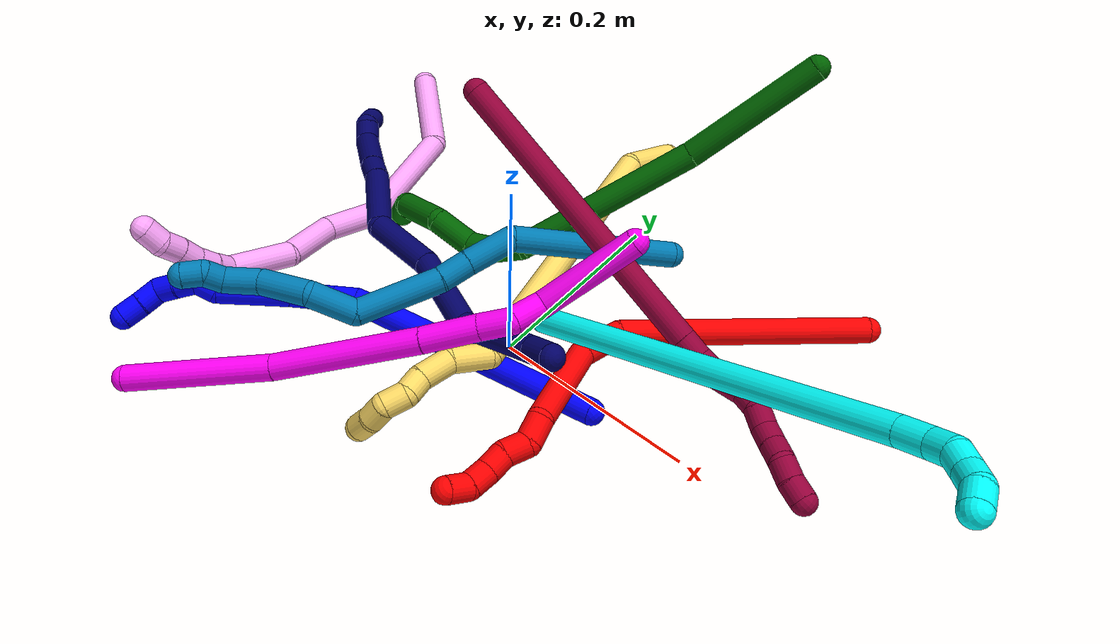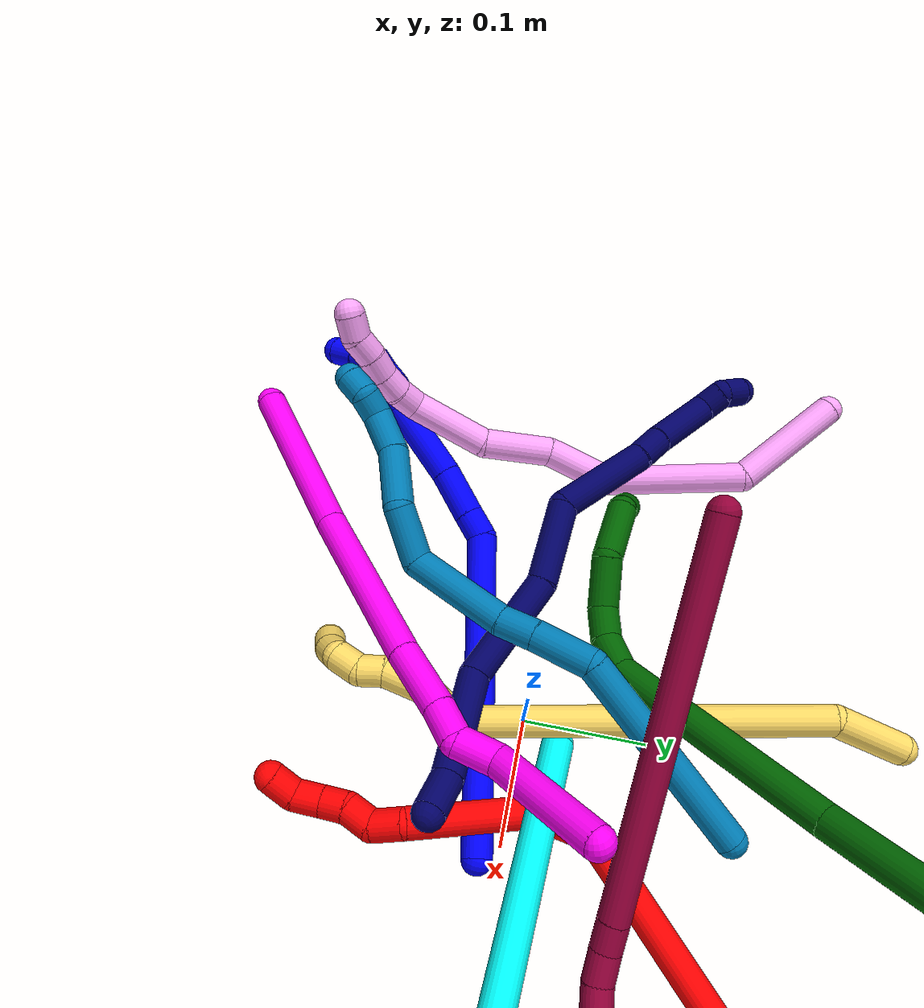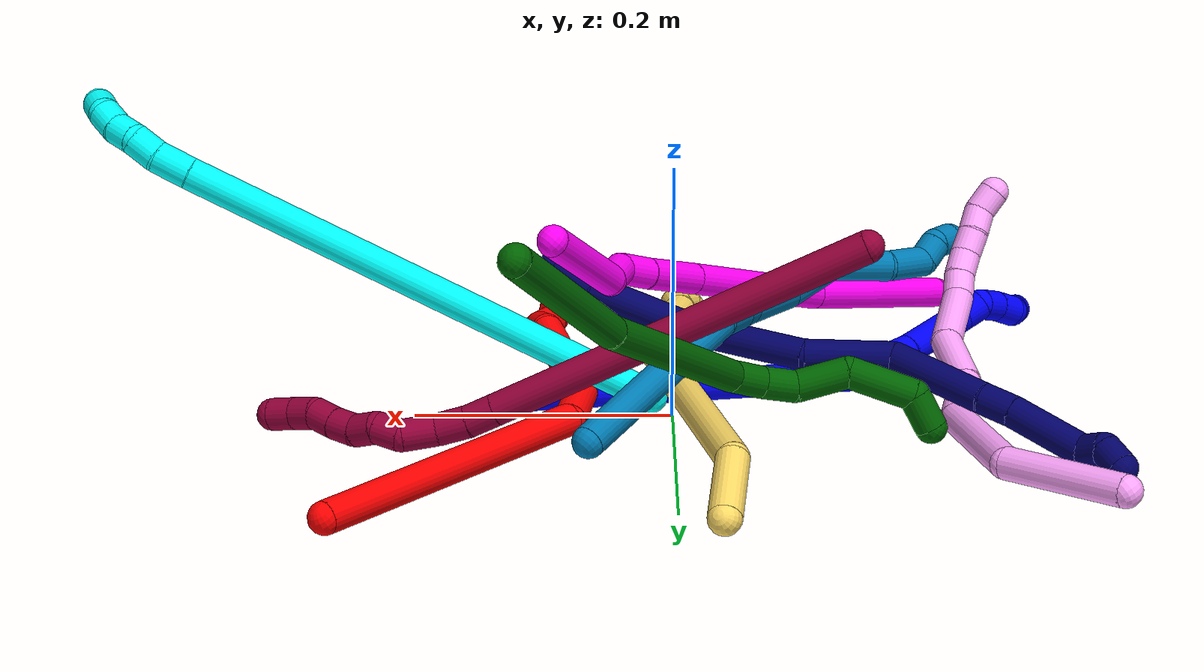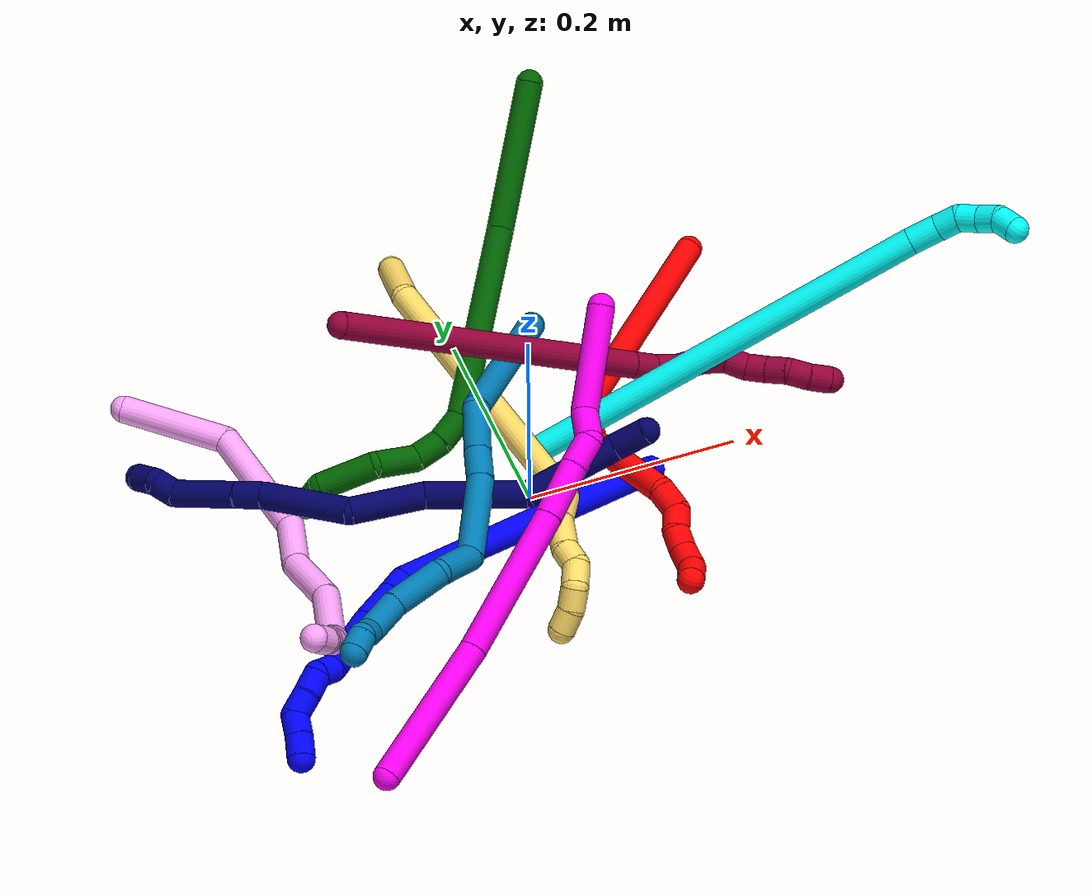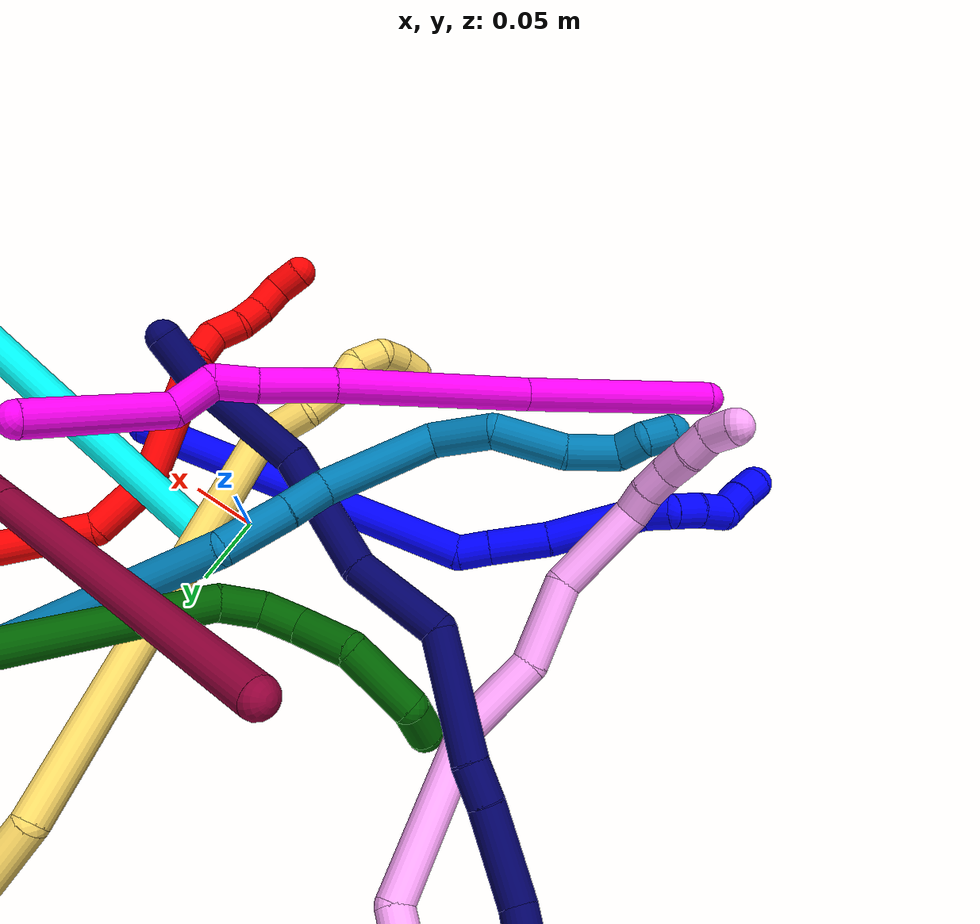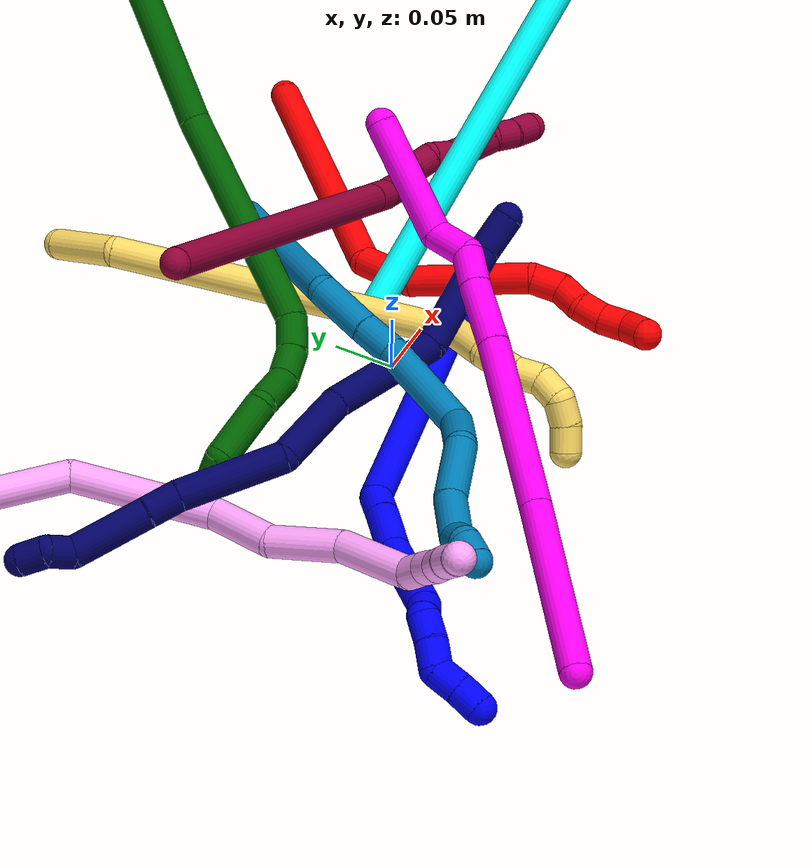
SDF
<sdf version="1.7">
 <world name="default">
  <plugin name="TubeGeneratorPlugin" filename="libtube_generator_plugin.so"/>
  <model name="photoneo_s_sensor">
   <static>1</static>
   <pose>0 0 2 1.57079 1.57079 3.14159</pose>
   <link name="link">
    <inertial><mass>0.1</mass></inertial>
    <sensor name="sensor" type="depth">
     <update_rate>30</update_rate>
     <camera>
      <horizontal_fov>1.22</horizontal_fov>
      <image><width>1920</width><height>1200</height><format>B8G8R8</format></image>
      <clip><near>0.1</near><far>4</far></clip>
      <depth_camera><output>points</output></depth_camera>
     </camera>
     <plugin name="camera_plugin" filename="libgazebo_ros_depth_camera.so">
      <baseline>0.2</baseline>
      <alwaysOn>1</alwaysOn>
      <updateRate>0.0</updateRate>
      <cameraName>camera_ir</cameraName>
      <imageTopicName>/camera/color/image_raw</imageTopicName>
      <cameraInfoTopicName>/camera/color/camera_info</cameraInfoTopicName>
      <depthImageTopicName>/camera/depth/image_raw</depthImageTopicName>
      <depthImageCameraInfoTopicName>/camera/depth/camera_info</depthImageCameraInfoTopicName>
      <pointCloudTopicName>/camera/depth/points</pointCloudTopicName>
      <frameName>fr_optical</frameName>
      <pointCloudCutoff>0.1</pointCloudCutoff>
      <pointCloudCutoffMax>2.0</pointCloudCutoffMax>
      <distortionK1>0</distortionK1>
      <distortionK2>0</distortionK2>
      <distortionK3>0</distortionK3>
      <distortionT1>0</distortionT1>
      <distortionT2>0</distortionT2>
      <CxPrime>0</CxPrime>
      <Cx>0</Cx>
      <Cy>0</Cy>
      <focalLength>0</focalLength>
      <hackBaseline>0</hackBaseline>
     </plugin>
    </sensor>
   </link>
  </model>
  <gravity>0 0 -9.8</gravity>
  <magnetic_field>6e-06 2.3e-05 -4.2e-05</magnetic_field>
  <atmosphere type="adiabatic"/>
  <physics name="default_physics" default="0" type="ode">
   <max_step_size>0.003</max_step_size>
   <real_time_factor>1</real_time_factor>
   <real_time_update_rate>1000</real_time_update_rate>
   <max_contacts>10000</max_contacts>
   <ode>
    <solver>
     <type>quick</type>
     <iters>100</iters>
     <sor>1.3</sor>
     <use_dynamic_moi_rescaling>0</use_dynamic_moi_rescaling>
    </solver>
    <constraints>
     <contact_max_correcting_vel>0</contact_max_correcting_vel>
     <contact_surface_layer>0.001</contact_surface_layer>
     <cfm>0</cfm>
     <erp>0.2</erp>
    </constraints>
   </ode>
  </physics>
  <scene><ambient>0.4 0.4 0.4 1</ambient><background>0.7 0.7 0.7 1</background><shadows>0</shadows></scene>
  <audio><device>default</device></audio>
  <spherical_coordinates>
   <surface_model>EARTH_WGS84</surface_model>
   <latitude_deg>0</latitude_deg>
   <longitude_deg>0</longitude_deg>
   <elevation>0</elevation>
   <heading_deg>0</heading_deg>
  </spherical_coordinates>
  <model name="bin">
   <static>1</static>
   <link name="bottom">
    <collision name="collision-bottom">
     <pose>0 0 -0.01 0 -0 0</pose>
     <geometry><box><size>0.8 0.6 0.02</size></box></geometry>
     <surface>
      <friction><ode><mu>100</mu><mu2>100</mu2></ode></friction>
      <contact><collide_bitmask>65535</collide_bitmask></contact>
     </surface>
    </collision>
   </link>
   <link name="west_wall">
    <collision name="collision-west_wall">
     <pose>-0.41 0 0.1 0 -0 0</pose>
     <geometry><box><size>0.02 0.6 0.2</size></box></geometry>
     <surface>
      <friction><ode><mu>100</mu><mu2>100</mu2></ode></friction>
      <contact><collide_bitmask>65535</collide_bitmask></contact>
     </surface>
    </collision>
   </link>
   <link name="east_wall">
    <collision name="collision-east_wall">
     <pose>0.41 0 0.1 0 -0 0</pose>
     <geometry><box><size>0.02 0.6 0.2</size></box></geometry>
     <surface>
      <friction><ode><mu>100</mu><mu2>100</mu2></ode></friction>
      <contact><collide_bitmask>65535</collide_bitmask></contact>
     </surface>
    </collision>
   </link>
   <link name="south_wall">
    <collision name="collision-south_wall">
     <pose>0 -0.31 0.1 0 -0 0</pose>
     <geometry><box><size>0.8 0.02 0.2</size></box></geometry>
     <surface>
      <friction><ode><mu>100</mu><mu2>100</mu2></ode></friction>
      <contact><collide_bitmask>65535</collide_bitmask></contact>
     </surface>
    </collision>
   </link>
   <link name="north_wall">
    <collision name="collision-north_wall">
     <pose>0 0.31 0.1 0 -0 0</pose>
     <geometry><box><size>0.8 0.02 0.2</size></box></geometry>
     <surface>
      <friction><ode><mu>100</mu><mu2>100</mu2></ode></friction>
      <contact><collide_bitmask>65535</collide_bitmask></contact>
     </surface>
    </collision>
   </link>
  </model>
  <model name="1">
   <static>0</static>
   <link name="1">
    <collision name="collision-cylinder-e_1_1_4">
     <pose>-0.068528 -0.006735 0.110316 0.060974 -0.555024 -0.017374</pose>
     <geometry><cylinder><radius>0.0125</radius><length>0.260085</length></cylinder></geometry>
     <surface>
      <friction><ode><mu>1.16</mu><mu2>1.16</mu2><slip1>0</slip1><slip2>0</slip2></ode></friction>
      <contact><ode><kp>1e+06</kp><kd>1</kd><max_vel>0</max_vel><min_depth>0.001</min_depth></ode></contact>
     </surface>
    </collision>
    <visual name="visual-cylinder-e_1_1_4">
     <pose>-0.068528 -0.006735 0.110316 0.060974 -0.555024 -0.017374</pose>
     <geometry><cylinder><radius>0.0125</radius><length>0.260085</length></cylinder></geometry>
     <material><ambient>0 0 1 1</ambient></material>
    </visual>
    <collision name="collision-cylinder-e_2_4_5">
     <pose>-0.142774 -0.019883 0.228194 0.703377 -0.523195 -0.195857</pose>
     <geometry><cylinder><radius>0.0125</radius><length>0.022893</length></cylinder></geometry>
     <surface>
      <friction><ode><mu>1.16</mu><mu2>1.16</mu2><slip1>0</slip1><slip2>0</slip2></ode></friction>
      <contact><ode><kp>1e+06</kp><kd>1</kd><max_vel>0</max_vel><min_depth>0.001</min_depth></ode></contact>
     </surface>
    </collision>
    <visual name="visual-cylinder-e_2_4_5">
     <pose>-0.142774 -0.019883 0.228194 0.703377 -0.523195 -0.195857</pose>
     <geometry><cylinder><radius>0.0125</radius><length>0.022893</length></cylinder></geometry>
     <material><ambient>0 0 1 1</ambient></material>
    </visual>
    <collision name="collision-cylinder-e_3_5_6">
     <pose>-0.159322 -0.037486 0.24979 0.673134 -0.542824 -0.194116</pose>
     <geometry><cylinder><radius>0.0125</radius><length>0.041925</length></cylinder></geometry>
     <surface>
      <friction><ode><mu>1.16</mu><mu2>1.16</mu2><slip1>0</slip1><slip2>0</slip2></ode></friction>
      <contact><ode><kp>1e+06</kp><kd>1</kd><max_vel>0</max_vel><min_depth>0.001</min_depth></ode></contact>
     </surface>
    </collision>
    <visual name="visual-cylinder-e_3_5_6">
     <pose>-0.159322 -0.037486 0.24979 0.673134 -0.542824 -0.194116</pose>
     <geometry><cylinder><radius>0.0125</radius><length>0.041925</length></cylinder></geometry>
     <material><ambient>0 0 1 1</ambient></material>
    </visual>
    <collision name="collision-cylinder-e_4_6_7">
     <pose>-0.186532 -0.07114 0.285555 0.801989 -0.482768 -0.207994</pose>
     <geometry><cylinder><radius>0.0125</radius><length>0.070574</length></cylinder></geometry>
     <surface>
      <friction><ode><mu>1.16</mu><mu2>1.16</mu2><slip1>0</slip1><slip2>0</slip2></ode></friction>
      <contact><ode><kp>1e+06</kp><kd>1</kd><max_vel>0</max_vel><min_depth>0.001</min_depth></ode></contact>
     </surface>
    </collision>
    <visual name="visual-cylinder-e_4_6_7">
     <pose>-0.186532 -0.07114 0.285555 0.801989 -0.482768 -0.207994</pose>
     <geometry><cylinder><radius>0.0125</radius><length>0.070574</length></cylinder></geometry>
     <material><ambient>0 0 1 1</ambient></material>
    </visual>
    <collision name="collision-cylinder-e_5_7_8">
     <pose>-0.205017 -0.097925 0.316243 0.449488 -0.208418 -0.04781</pose>
     <geometry><cylinder><radius>0.0125</radius><length>0.020331</length></cylinder></geometry>
     <surface>
      <friction><ode><mu>1.16</mu><mu2>1.16</mu2><slip1>0</slip1><slip2>0</slip2></ode></friction>
      <contact><ode><kp>1e+06</kp><kd>1</kd><max_vel>0</max_vel><min_depth>0.001</min_depth></ode></contact>
     </surface>
    </collision>
    <visual name="visual-cylinder-e_5_7_8">
     <pose>-0.205017 -0.097925 0.316243 0.449488 -0.208418 -0.04781</pose>
     <geometry><cylinder><radius>0.0125</radius><length>0.020331</length></cylinder></geometry>
     <material><ambient>0 0 1 1</ambient></material>
    </visual>
    <collision name="collision-cylinder-e_6_8_9">
     <pose>-0.215464 -0.106628 0.32957 0.78667 -0.932745 -0.411867</pose>
     <geometry><cylinder><radius>0.0125</radius><length>0.020776</length></cylinder></geometry>
     <surface>
      <friction><ode><mu>1.16</mu><mu2>1.16</mu2><slip1>0</slip1><slip2>0</slip2></ode></friction>
      <contact><ode><kp>1e+06</kp><kd>1</kd><max_vel>0</max_vel><min_depth>0.001</min_depth></ode></contact>
     </surface>
    </collision>
    <visual name="visual-cylinder-e_6_8_9">
     <pose>-0.215464 -0.106628 0.32957 0.78667 -0.932745 -0.411867</pose>
     <geometry><cylinder><radius>0.0125</radius><length>0.020776</length></cylinder></geometry>
     <material><ambient>0 0 1 1</ambient></material>
    </visual>
    <collision name="collision-cylinder-e_7_9_10">
     <pose>-0.233201 -0.114118 0.338384 0.610537 -1.0471 -0.359892</pose>
     <geometry><cylinder><radius>0.0125</radius><length>0.021693</length></cylinder></geometry>
     <surface>
      <friction><ode><mu>1.16</mu><mu2>1.16</mu2><slip1>0</slip1><slip2>0</slip2></ode></friction>
      <contact><ode><kp>1e+06</kp><kd>1</kd><max_vel>0</max_vel><min_depth>0.001</min_depth></ode></contact>
     </surface>
    </collision>
    <visual name="visual-cylinder-e_7_9_10">
     <pose>-0.233201 -0.114118 0.338384 0.610537 -1.0471 -0.359892</pose>
     <geometry><cylinder><radius>0.0125</radius><length>0.021693</length></cylinder></geometry>
     <material><ambient>0 0 1 1</ambient></material>
    </visual>
    <collision name="collision-cylinder-e_8_10_11">
     <pose>-0.24944 -0.125272 0.342079 1.66365 -0.702917 -0.765175</pose>
     <geometry><cylinder><radius>0.0125</radius><length>0.021179</length></cylinder></geometry>
     <surface>
      <friction><ode><mu>1.16</mu><mu2>1.16</mu2><slip1>0</slip1><slip2>0</slip2></ode></friction>
      <contact><ode><kp>1e+06</kp><kd>1</kd><max_vel>0</max_vel><min_depth>0.001</min_depth></ode></contact>
     </surface>
    </collision>
    <visual name="visual-cylinder-e_8_10_11">
     <pose>-0.24944 -0.125272 0.342079 1.66365 -0.702917 -0.765175</pose>
     <geometry><cylinder><radius>0.0125</radius><length>0.021179</length></cylinder></geometry>
     <material><ambient>0 0 1 1</ambient></material>
    </visual>
    <collision name="collision-cylinder-e_9_11_2">
     <pose>-0.26342 -0.140705 0.341253 1.58118 -0.767898 -0.775138</pose>
     <geometry><cylinder><radius>0.0125</radius><length>0.020544</length></cylinder></geometry>
     <surface>
      <friction><ode><mu>1.16</mu><mu2>1.16</mu2><slip1>0</slip1><slip2>0</slip2></ode></friction>
      <contact><ode><kp>1e+06</kp><kd>1</kd><max_vel>0</max_vel><min_depth>0.001</min_depth></ode></contact>
     </surface>
    </collision>
    <visual name="visual-cylinder-e_9_11_2">
     <pose>-0.26342 -0.140705 0.341253 1.58118 -0.767898 -0.775138</pose>
     <geometry><cylinder><radius>0.0125</radius><length>0.020544</length></cylinder></geometry>
     <material><ambient>0 0 1 1</ambient></material>
    </visual>
    <collision name="collision-sphere-2">
     <pose>-0.270555 -0.148094 0.341177 0 -0 0</pose>
     <geometry><sphere><radius>0.0125</radius></sphere></geometry>
     <surface>
      <friction><ode><mu>1.16</mu><mu2>1.16</mu2><slip1>0</slip1><slip2>0</slip2></ode></friction>
      <contact><ode><kp>1e+06</kp><kd>1</kd><max_vel>0</max_vel><min_depth>0.001</min_depth></ode></contact>
     </surface>
    </collision>
    <visual name="visual-sphere-2">
     <pose>-0.270555 -0.148094 0.341177 0 -0 0</pose>
     <geometry><sphere><radius>0.0125</radius></sphere></geometry>
     <material><ambient>0 0 1 1</ambient></material>
    </visual>
    <collision name="collision-sphere-11">
     <pose>-0.256285 -0.133316 0.34133 0 -0 0</pose>
     <geometry><sphere><radius>0.0125</radius></sphere></geometry>
     <surface>
      <friction><ode><mu>1.16</mu><mu2>1.16</mu2><slip1>0</slip1><slip2>0</slip2></ode></friction>
      <contact><ode><kp>1e+06</kp><kd>1</kd><max_vel>0</max_vel><min_depth>0.001</min_depth></ode></contact>
     </surface>
    </collision>
    <visual name="visual-sphere-11">
     <pose>-0.256285 -0.133316 0.34133 0 -0 0</pose>
     <geometry><sphere><radius>0.0125</radius></sphere></geometry>
     <material><ambient>0 0 1 1</ambient></material>
    </visual>
    <collision name="collision-sphere-10">
     <pose>-0.242594 -0.117228 0.342828 0 -0 0</pose>
     <geometry><sphere><radius>0.0125</radius></sphere></geometry>
     <surface>
      <friction><ode><mu>1.16</mu><mu2>1.16</mu2><slip1>0</slip1><slip2>0</slip2></ode></friction>
      <contact><ode><kp>1e+06</kp><kd>1</kd><max_vel>0</max_vel><min_depth>0.001</min_depth></ode></contact>
     </surface>
    </collision>
    <visual name="visual-sphere-10">
     <pose>-0.242594 -0.117228 0.342828 0 -0 0</pose>
     <geometry><sphere><radius>0.0125</radius></sphere></geometry>
     <material><ambient>0 0 1 1</ambient></material>
    </visual>
    <collision name="collision-sphere-9">
     <pose>-0.223809 -0.111008 0.33394 0 -0 0</pose>
     <geometry><sphere><radius>0.0125</radius></sphere></geometry>
     <surface>
      <friction><ode><mu>1.16</mu><mu2>1.16</mu2><slip1>0</slip1><slip2>0</slip2></ode></friction>
      <contact><ode><kp>1e+06</kp><kd>1</kd><max_vel>0</max_vel><min_depth>0.001</min_depth></ode></contact>
     </surface>
    </collision>
    <visual name="visual-sphere-9">
     <pose>-0.223809 -0.111008 0.33394 0 -0 0</pose>
     <geometry><sphere><radius>0.0125</radius></sphere></geometry>
     <material><ambient>0 0 1 1</ambient></material>
    </visual>
    <collision name="collision-sphere-4">
     <pose>-0.137055 -0.01347 0.220632 0 -0 0</pose>
     <geometry><sphere><radius>0.0125</radius></sphere></geometry>
     <surface>
      <friction><ode><mu>1.16</mu><mu2>1.16</mu2><slip1>0</slip1><slip2>0</slip2></ode></friction>
      <contact><ode><kp>1e+06</kp><kd>1</kd><max_vel>0</max_vel><min_depth>0.001</min_depth></ode></contact>
     </surface>
    </collision>
    <visual name="visual-sphere-4">
     <pose>-0.137055 -0.01347 0.220632 0 -0 0</pose>
     <geometry><sphere><radius>0.0125</radius></sphere></geometry>
     <material><ambient>0 0 1 1</ambient></material>
    </visual>
    <collision name="collision-sphere-1">
     <geometry><sphere><radius>0.0125</radius></sphere></geometry>
     <surface>
      <friction><ode><mu>1.16</mu><mu2>1.16</mu2><slip1>0</slip1><slip2>0</slip2></ode></friction>
      <contact><ode><kp>1e+06</kp><kd>1</kd><max_vel>0</max_vel><min_depth>0.001</min_depth></ode></contact>
     </surface>
    </collision>
    <visual name="visual-sphere-1">
     <geometry><sphere><radius>0.0125</radius></sphere></geometry>
     <material><ambient>0 0 1 1</ambient></material>
    </visual>
    <collision name="collision-sphere-8">
     <pose>-0.20712 -0.102247 0.325201 0 -0 0</pose>
     <geometry><sphere><radius>0.0125</radius></sphere></geometry>
     <surface>
      <friction><ode><mu>1.16</mu><mu2>1.16</mu2><slip1>0</slip1><slip2>0</slip2></ode></friction>
      <contact><ode><kp>1e+06</kp><kd>1</kd><max_vel>0</max_vel><min_depth>0.001</min_depth></ode></contact>
     </surface>
    </collision>
    <visual name="visual-sphere-8">
     <pose>-0.20712 -0.102247 0.325201 0 -0 0</pose>
     <geometry><sphere><radius>0.0125</radius></sphere></geometry>
     <material><ambient>0 0 1 1</ambient></material>
    </visual>
    <collision name="collision-sphere-5">
     <pose>-0.148494 -0.026296 0.235756 0 -0 0</pose>
     <geometry><sphere><radius>0.0125</radius></sphere></geometry>
     <surface>
      <friction><ode><mu>1.16</mu><mu2>1.16</mu2><slip1>0</slip1><slip2>0</slip2></ode></friction>
      <contact><ode><kp>1e+06</kp><kd>1</kd><max_vel>0</max_vel><min_depth>0.001</min_depth></ode></contact>
     </surface>
    </collision>
    <visual name="visual-sphere-5">
     <pose>-0.148494 -0.026296 0.235756 0 -0 0</pose>
     <geometry><sphere><radius>0.0125</radius></sphere></geometry>
     <material><ambient>0 0 1 1</ambient></material>
    </visual>
    <collision name="collision-sphere-6">
     <pose>-0.170151 -0.048677 0.263825 0 -0 0</pose>
     <geometry><sphere><radius>0.0125</radius></sphere></geometry>
     <surface>
      <friction><ode><mu>1.16</mu><mu2>1.16</mu2><slip1>0</slip1><slip2>0</slip2></ode></friction>
      <contact><ode><kp>1e+06</kp><kd>1</kd><max_vel>0</max_vel><min_depth>0.001</min_depth></ode></contact>
     </surface>
    </collision>
    <visual name="visual-sphere-6">
     <pose>-0.170151 -0.048677 0.263825 0 -0 0</pose>
     <geometry><sphere><radius>0.0125</radius></sphere></geometry>
     <material><ambient>0 0 1 1</ambient></material>
    </visual>
    <collision name="collision-sphere-7">
     <pose>-0.202913 -0.093604 0.307285 0 -0 0</pose>
     <geometry><sphere><radius>0.0125</radius></sphere></geometry>
     <surface>
      <friction><ode><mu>1.16</mu><mu2>1.16</mu2><slip1>0</slip1><slip2>0</slip2></ode></friction>
      <contact><ode><kp>1e+06</kp><kd>1</kd><max_vel>0</max_vel><min_depth>0.001</min_depth></ode></contact>
     </surface>
    </collision>
    <visual name="visual-sphere-7">
     <pose>-0.202913 -0.093604 0.307285 0 -0 0</pose>
     <geometry><sphere><radius>0.0125</radius></sphere></geometry>
     <material><ambient>0 0 1 1</ambient></material>
    </visual>
    <inertial>
     <pose>-0.130667 -0.042049 0.198827 0 -0 0</pose>
     <mass>0.5</mass>
     <inertia>
      <ixx>0.001242</ixx>
      <ixy>0</ixy>
      <ixz>0</ixz>
      <iyy>0.001469</iyy>
      <iyz>0</iyz>
      <izz>0.000936</izz>
     </inertia>
    </inertial>
   </link>
   <pose>0.111741 -0.015909 0.011489 -0.670616 -0.923237 0.686735</pose>
  </model>
  <model name="2">
   <static>0</static>
   <link name="2">
    <collision name="collision-cylinder-e_1_1_4">
     <pose>-0.089848 -0.05931 -0.052337 2.29382 -0.848929 -1.57234</pose>
     <geometry><cylinder><radius>0.0125</radius><length>0.239412</length></cylinder></geometry>
     <surface>
      <friction><ode><mu>1.16</mu><mu2>1.16</mu2><slip1>0</slip1><slip2>0</slip2></ode></friction>
      <contact><ode><kp>1e+06</kp><kd>1</kd><max_vel>0</max_vel><min_depth>0.001</min_depth></ode></contact>
     </surface>
    </collision>
    <visual name="visual-cylinder-e_1_1_4">
     <pose>-0.089848 -0.05931 -0.052337 2.29382 -0.848929 -1.57234</pose>
     <geometry><cylinder><radius>0.0125</radius><length>0.239412</length></cylinder></geometry>
     <material><ambient>1 0 0 1</ambient></material>
    </visual>
    <collision name="collision-cylinder-e_2_4_5">
     <pose>-0.188229 -0.139937 -0.110055 1.81805 -0.370204 -0.471813</pose>
     <geometry><cylinder><radius>0.0125</radius><length>0.047167</length></cylinder></geometry>
     <surface>
      <friction><ode><mu>1.16</mu><mu2>1.16</mu2><slip1>0</slip1><slip2>0</slip2></ode></friction>
      <contact><ode><kp>1e+06</kp><kd>1</kd><max_vel>0</max_vel><min_depth>0.001</min_depth></ode></contact>
     </surface>
    </collision>
    <visual name="visual-cylinder-e_2_4_5">
     <pose>-0.188229 -0.139937 -0.110055 1.81805 -0.370204 -0.471813</pose>
     <geometry><cylinder><radius>0.0125</radius><length>0.047167</length></cylinder></geometry>
     <material><ambient>1 0 0 1</ambient></material>
    </visual>
    <collision name="collision-cylinder-e_3_5_6">
     <pose>-0.197412 -0.210895 -0.111248 1.48662 -0.013047 -0.011993</pose>
     <geometry><cylinder><radius>0.0125</radius><length>0.099643</length></cylinder></geometry>
     <surface>
      <friction><ode><mu>1.16</mu><mu2>1.16</mu2><slip1>0</slip1><slip2>0</slip2></ode></friction>
      <contact><ode><kp>1e+06</kp><kd>1</kd><max_vel>0</max_vel><min_depth>0.001</min_depth></ode></contact>
     </surface>
    </collision>
    <visual name="visual-cylinder-e_3_5_6">
     <pose>-0.197412 -0.210895 -0.111248 1.48662 -0.013047 -0.011993</pose>
     <geometry><cylinder><radius>0.0125</radius><length>0.099643</length></cylinder></geometry>
     <material><ambient>1 0 0 1</ambient></material>
    </visual>
    <collision name="collision-cylinder-e_4_6_7">
     <pose>-0.195968 -0.272334 -0.111046 1.89663 0.166608 0.23165</pose>
     <geometry><cylinder><radius>0.0125</radius><length>0.025255</length></cylinder></geometry>
     <surface>
      <friction><ode><mu>1.16</mu><mu2>1.16</mu2><slip1>0</slip1><slip2>0</slip2></ode></friction>
      <contact><ode><kp>1e+06</kp><kd>1</kd><max_vel>0</max_vel><min_depth>0.001</min_depth></ode></contact>
     </surface>
    </collision>
    <visual name="visual-cylinder-e_4_6_7">
     <pose>-0.195968 -0.272334 -0.111046 1.89663 0.166608 0.23165</pose>
     <geometry><cylinder><radius>0.0125</radius><length>0.025255</length></cylinder></geometry>
     <material><ambient>1 0 0 1</ambient></material>
    </visual>
    <collision name="collision-cylinder-e_5_7_8">
     <pose>-0.199075 -0.292738 -0.120418 2.12994 -0.473398 -0.821462</pose>
     <geometry><cylinder><radius>0.0125</radius><length>0.022816</length></cylinder></geometry>
     <surface>
      <friction><ode><mu>1.16</mu><mu2>1.16</mu2><slip1>0</slip1><slip2>0</slip2></ode></friction>
      <contact><ode><kp>1e+06</kp><kd>1</kd><max_vel>0</max_vel><min_depth>0.001</min_depth></ode></contact>
     </surface>
    </collision>
    <visual name="visual-cylinder-e_5_7_8">
     <pose>-0.199075 -0.292738 -0.120418 2.12994 -0.473398 -0.821462</pose>
     <geometry><cylinder><radius>0.0125</radius><length>0.022816</length></cylinder></geometry>
     <material><ambient>1 0 0 1</ambient></material>
    </visual>
    <collision name="collision-cylinder-e_6_8_9">
     <pose>-0.205334 -0.310709 -0.130351 2.02289 -0.101318 -0.161623</pose>
     <geometry><cylinder><radius>0.0125</radius><length>0.020927</length></cylinder></geometry>
     <surface>
      <friction><ode><mu>1.16</mu><mu2>1.16</mu2><slip1>0</slip1><slip2>0</slip2></ode></friction>
      <contact><ode><kp>1e+06</kp><kd>1</kd><max_vel>0</max_vel><min_depth>0.001</min_depth></ode></contact>
     </surface>
    </collision>
    <visual name="visual-cylinder-e_6_8_9">
     <pose>-0.205334 -0.310709 -0.130351 2.02289 -0.101318 -0.161623</pose>
     <geometry><cylinder><radius>0.0125</radius><length>0.020927</length></cylinder></geometry>
     <material><ambient>1 0 0 1</ambient></material>
    </visual>
    <collision name="collision-cylinder-e_7_9_10">
     <pose>-0.208925 -0.330982 -0.137009 1.76187 -0.224134 -0.271115</pose>
     <geometry><cylinder><radius>0.0125</radius><length>0.022793</length></cylinder></geometry>
     <surface>
      <friction><ode><mu>1.16</mu><mu2>1.16</mu2><slip1>0</slip1><slip2>0</slip2></ode></friction>
      <contact><ode><kp>1e+06</kp><kd>1</kd><max_vel>0</max_vel><min_depth>0.001</min_depth></ode></contact>
     </surface>
    </collision>
    <visual name="visual-cylinder-e_7_9_10">
     <pose>-0.208925 -0.330982 -0.137009 1.76187 -0.224134 -0.271115</pose>
     <geometry><cylinder><radius>0.0125</radius><length>0.022793</length></cylinder></geometry>
     <material><ambient>1 0 0 1</ambient></material>
    </visual>
    <collision name="collision-cylinder-e_8_10_2">
     <pose>-0.218537 -0.350243 -0.140112 1.68918 -0.699631 -0.779531</pose>
     <geometry><cylinder><radius>0.0125</radius><length>0.021987</length></cylinder></geometry>
     <surface>
      <friction><ode><mu>1.16</mu><mu2>1.16</mu2><slip1>0</slip1><slip2>0</slip2></ode></friction>
      <contact><ode><kp>1e+06</kp><kd>1</kd><max_vel>0</max_vel><min_depth>0.001</min_depth></ode></contact>
     </surface>
    </collision>
    <visual name="visual-cylinder-e_8_10_2">
     <pose>-0.218537 -0.350243 -0.140112 1.68918 -0.699631 -0.779531</pose>
     <geometry><cylinder><radius>0.0125</radius><length>0.021987</length></cylinder></geometry>
     <material><ambient>1 0 0 1</ambient></material>
    </visual>
    <collision name="collision-sphere-2">
     <pose>-0.225616 -0.358595 -0.141105 0 -0 0</pose>
     <geometry><sphere><radius>0.0125</radius></sphere></geometry>
     <surface>
      <friction><ode><mu>1.16</mu><mu2>1.16</mu2><slip1>0</slip1><slip2>0</slip2></ode></friction>
      <contact><ode><kp>1e+06</kp><kd>1</kd><max_vel>0</max_vel><min_depth>0.001</min_depth></ode></contact>
     </surface>
    </collision>
    <visual name="visual-sphere-2">
     <pose>-0.225616 -0.358595 -0.141105 0 -0 0</pose>
     <geometry><sphere><radius>0.0125</radius></sphere></geometry>
     <material><ambient>1 0 0 1</ambient></material>
    </visual>
    <collision name="collision-sphere-10">
     <pose>-0.211458 -0.341891 -0.139119 0 -0 0</pose>
     <geometry><sphere><radius>0.0125</radius></sphere></geometry>
     <surface>
      <friction><ode><mu>1.16</mu><mu2>1.16</mu2><slip1>0</slip1><slip2>0</slip2></ode></friction>
      <contact><ode><kp>1e+06</kp><kd>1</kd><max_vel>0</max_vel><min_depth>0.001</min_depth></ode></contact>
     </surface>
    </collision>
    <visual name="visual-sphere-10">
     <pose>-0.211458 -0.341891 -0.139119 0 -0 0</pose>
     <geometry><sphere><radius>0.0125</radius></sphere></geometry>
     <material><ambient>1 0 0 1</ambient></material>
    </visual>
    <collision name="collision-sphere-9">
     <pose>-0.206392 -0.320073 -0.134898 0 -0 0</pose>
     <geometry><sphere><radius>0.0125</radius></sphere></geometry>
     <surface>
      <friction><ode><mu>1.16</mu><mu2>1.16</mu2><slip1>0</slip1><slip2>0</slip2></ode></friction>
      <contact><ode><kp>1e+06</kp><kd>1</kd><max_vel>0</max_vel><min_depth>0.001</min_depth></ode></contact>
     </surface>
    </collision>
    <visual name="visual-sphere-9">
     <pose>-0.206392 -0.320073 -0.134898 0 -0 0</pose>
     <geometry><sphere><radius>0.0125</radius></sphere></geometry>
     <material><ambient>1 0 0 1</ambient></material>
    </visual>
    <collision name="collision-sphere-4">
     <pose>-0.179697 -0.11862 -0.104675 0 -0 0</pose>
     <geometry><sphere><radius>0.0125</radius></sphere></geometry>
     <surface>
      <friction><ode><mu>1.16</mu><mu2>1.16</mu2><slip1>0</slip1><slip2>0</slip2></ode></friction>
      <contact><ode><kp>1e+06</kp><kd>1</kd><max_vel>0</max_vel><min_depth>0.001</min_depth></ode></contact>
     </surface>
    </collision>
    <visual name="visual-sphere-4">
     <pose>-0.179697 -0.11862 -0.104675 0 -0 0</pose>
     <geometry><sphere><radius>0.0125</radius></sphere></geometry>
     <material><ambient>1 0 0 1</ambient></material>
    </visual>
    <collision name="collision-sphere-1">
     <geometry><sphere><radius>0.0125</radius></sphere></geometry>
     <surface>
      <friction><ode><mu>1.16</mu><mu2>1.16</mu2><slip1>0</slip1><slip2>0</slip2></ode></friction>
      <contact><ode><kp>1e+06</kp><kd>1</kd><max_vel>0</max_vel><min_depth>0.001</min_depth></ode></contact>
     </surface>
    </collision>
    <visual name="visual-sphere-1">
     <geometry><sphere><radius>0.0125</radius></sphere></geometry>
     <material><ambient>1 0 0 1</ambient></material>
    </visual>
    <collision name="collision-sphere-8">
     <pose>-0.204276 -0.301345 -0.125803 0 -0 0</pose>
     <geometry><sphere><radius>0.0125</radius></sphere></geometry>
     <surface>
      <friction><ode><mu>1.16</mu><mu2>1.16</mu2><slip1>0</slip1><slip2>0</slip2></ode></friction>
      <contact><ode><kp>1e+06</kp><kd>1</kd><max_vel>0</max_vel><min_depth>0.001</min_depth></ode></contact>
     </surface>
    </collision>
    <visual name="visual-sphere-8">
     <pose>-0.204276 -0.301345 -0.125803 0 -0 0</pose>
     <geometry><sphere><radius>0.0125</radius></sphere></geometry>
     <material><ambient>1 0 0 1</ambient></material>
    </visual>
    <collision name="collision-sphere-5">
     <pose>-0.196762 -0.161255 -0.115436 0 -0 0</pose>
     <geometry><sphere><radius>0.0125</radius></sphere></geometry>
     <surface>
      <friction><ode><mu>1.16</mu><mu2>1.16</mu2><slip1>0</slip1><slip2>0</slip2></ode></friction>
      <contact><ode><kp>1e+06</kp><kd>1</kd><max_vel>0</max_vel><min_depth>0.001</min_depth></ode></contact>
     </surface>
    </collision>
    <visual name="visual-sphere-5">
     <pose>-0.196762 -0.161255 -0.115436 0 -0 0</pose>
     <geometry><sphere><radius>0.0125</radius></sphere></geometry>
     <material><ambient>1 0 0 1</ambient></material>
    </visual>
    <collision name="collision-sphere-6">
     <pose>-0.198062 -0.260536 -0.10706 0 -0 0</pose>
     <geometry><sphere><radius>0.0125</radius></sphere></geometry>
     <surface>
      <friction><ode><mu>1.16</mu><mu2>1.16</mu2><slip1>0</slip1><slip2>0</slip2></ode></friction>
      <contact><ode><kp>1e+06</kp><kd>1</kd><max_vel>0</max_vel><min_depth>0.001</min_depth></ode></contact>
     </surface>
    </collision>
    <visual name="visual-sphere-6">
     <pose>-0.198062 -0.260536 -0.10706 0 -0 0</pose>
     <geometry><sphere><radius>0.0125</radius></sphere></geometry>
     <material><ambient>1 0 0 1</ambient></material>
    </visual>
    <collision name="collision-sphere-7">
     <pose>-0.193874 -0.284131 -0.115032 0 -0 0</pose>
     <geometry><sphere><radius>0.0125</radius></sphere></geometry>
     <surface>
      <friction><ode><mu>1.16</mu><mu2>1.16</mu2><slip1>0</slip1><slip2>0</slip2></ode></friction>
      <contact><ode><kp>1e+06</kp><kd>1</kd><max_vel>0</max_vel><min_depth>0.001</min_depth></ode></contact>
     </surface>
    </collision>
    <visual name="visual-sphere-7">
     <pose>-0.193874 -0.284131 -0.115032 0 -0 0</pose>
     <geometry><sphere><radius>0.0125</radius></sphere></geometry>
     <material><ambient>1 0 0 1</ambient></material>
    </visual>
    <inertial>
     <pose>-0.14683 -0.154236 -0.086579 0 -0 0</pose>
     <mass>0.5</mass>
     <inertia>
      <ixx>-0.000686</ixx>
      <ixy>0</ixy>
      <ixz>0</ixz>
      <iyy>-0.000142</iyy>
      <iyz>0</iyz>
      <izz>0.001536</izz>
     </inertia>
    </inertial>
   </link>
   <pose>0.249044 0.234905 0.012075 -0.139095 0.506045 0.194345</pose>
  </model>
  <model name="3">
   <static>0</static>
   <link name="3">
    <collision name="collision-cylinder-e_1_1_4">
     <pose>0.10415 0.00074 0.165022 -0.004487 0.562987 -0.001298</pose>
     <geometry><cylinder><radius>0.0125</radius><length>0.390282</length></cylinder></geometry>
     <surface>
      <friction><ode><mu>1.16</mu><mu2>1.16</mu2><slip1>0</slip1><slip2>0</slip2></ode></friction>
      <contact><ode><kp>1e+06</kp><kd>1</kd><max_vel>0</max_vel><min_depth>0.001</min_depth></ode></contact>
     </surface>
    </collision>
    <visual name="visual-cylinder-e_1_1_4">
     <pose>0.10415 0.00074 0.165022 -0.004487 0.562987 -0.001298</pose>
     <geometry><cylinder><radius>0.0125</radius><length>0.390282</length></cylinder></geometry>
     <material><ambient>0.003922 1 0.996078 1</ambient></material>
    </visual>
    <collision name="collision-cylinder-e_2_4_5">
     <pose>0.215695 0.000567 0.341902 0.07694 0.556303 0.02198</pose>
     <geometry><cylinder><radius>0.0125</radius><length>0.02801</length></cylinder></geometry>
     <surface>
      <friction><ode><mu>1.16</mu><mu2>1.16</mu2><slip1>0</slip1><slip2>0</slip2></ode></friction>
      <contact><ode><kp>1e+06</kp><kd>1</kd><max_vel>0</max_vel><min_depth>0.001</min_depth></ode></contact>
     </surface>
    </collision>
    <visual name="visual-cylinder-e_2_4_5">
     <pose>0.215695 0.000567 0.341902 0.07694 0.556303 0.02198</pose>
     <geometry><cylinder><radius>0.0125</radius><length>0.02801</length></cylinder></geometry>
     <material><ambient>0.003922 1 0.996078 1</ambient></material>
    </visual>
    <collision name="collision-cylinder-e_3_5_6">
     <pose>0.227274 -0.002559 0.363439 0.224656 0.398876 0.045593</pose>
     <geometry><cylinder><radius>0.0125</radius><length>0.021547</length></cylinder></geometry>
     <surface>
      <friction><ode><mu>1.16</mu><mu2>1.16</mu2><slip1>0</slip1><slip2>0</slip2></ode></friction>
      <contact><ode><kp>1e+06</kp><kd>1</kd><max_vel>0</max_vel><min_depth>0.001</min_depth></ode></contact>
     </surface>
    </collision>
    <visual name="visual-cylinder-e_3_5_6">
     <pose>0.227274 -0.002559 0.363439 0.224656 0.398876 0.045593</pose>
     <geometry><cylinder><radius>0.0125</radius><length>0.021547</length></cylinder></geometry>
     <material><ambient>0.003922 1 0.996078 1</ambient></material>
    </visual>
    <collision name="collision-cylinder-e_4_6_7">
     <pose>0.236619 -0.010546 0.379486 0.736621 0.54062 0.213061</pose>
     <geometry><cylinder><radius>0.0125</radius><length>0.020055</length></cylinder></geometry>
     <surface>
      <friction><ode><mu>1.16</mu><mu2>1.16</mu2><slip1>0</slip1><slip2>0</slip2></ode></friction>
      <contact><ode><kp>1e+06</kp><kd>1</kd><max_vel>0</max_vel><min_depth>0.001</min_depth></ode></contact>
     </surface>
    </collision>
    <visual name="visual-cylinder-e_4_6_7">
     <pose>0.236619 -0.010546 0.379486 0.736621 0.54062 0.213061</pose>
     <geometry><cylinder><radius>0.0125</radius><length>0.020055</length></cylinder></geometry>
     <material><ambient>0.003922 1 0.996078 1</ambient></material>
    </visual>
    <collision name="collision-cylinder-e_5_7_8">
     <pose>0.244802 -0.022676 0.392963 0.729437 0.306877 0.117957</pose>
     <geometry><cylinder><radius>0.0125</radius><length>0.020003</length></cylinder></geometry>
     <surface>
      <friction><ode><mu>1.16</mu><mu2>1.16</mu2><slip1>0</slip1><slip2>0</slip2></ode></friction>
      <contact><ode><kp>1e+06</kp><kd>1</kd><max_vel>0</max_vel><min_depth>0.001</min_depth></ode></contact>
     </surface>
    </collision>
    <visual name="visual-cylinder-e_5_7_8">
     <pose>0.244802 -0.022676 0.392963 0.729437 0.306877 0.117957</pose>
     <geometry><cylinder><radius>0.0125</radius><length>0.020003</length></cylinder></geometry>
     <material><ambient>0.003922 1 0.996078 1</ambient></material>
    </visual>
    <collision name="collision-cylinder-e_6_8_2">
     <pose>0.250577 -0.038133 0.403324 1.22753 0.277582 0.196201</pose>
     <geometry><cylinder><radius>0.0125</radius><length>0.020103</length></cylinder></geometry>
     <surface>
      <friction><ode><mu>1.16</mu><mu2>1.16</mu2><slip1>0</slip1><slip2>0</slip2></ode></friction>
      <contact><ode><kp>1e+06</kp><kd>1</kd><max_vel>0</max_vel><min_depth>0.001</min_depth></ode></contact>
     </surface>
    </collision>
    <visual name="visual-cylinder-e_6_8_2">
     <pose>0.250577 -0.038133 0.403324 1.22753 0.277582 0.196201</pose>
     <geometry><cylinder><radius>0.0125</radius><length>0.020103</length></cylinder></geometry>
     <material><ambient>0.003922 1 0.996078 1</ambient></material>
    </visual>
    <collision name="collision-sphere-2">
     <pose>0.253332 -0.047235 0.406578 0 -0 0</pose>
     <geometry><sphere><radius>0.0125</radius></sphere></geometry>
     <surface>
      <friction><ode><mu>1.16</mu><mu2>1.16</mu2><slip1>0</slip1><slip2>0</slip2></ode></friction>
      <contact><ode><kp>1e+06</kp><kd>1</kd><max_vel>0</max_vel><min_depth>0.001</min_depth></ode></contact>
     </surface>
    </collision>
    <visual name="visual-sphere-2">
     <pose>0.253332 -0.047235 0.406578 0 -0 0</pose>
     <geometry><sphere><radius>0.0125</radius></sphere></geometry>
     <material><ambient>0.003922 1 0.996078 1</ambient></material>
    </visual>
    <collision name="collision-sphere-4">
     <pose>0.208299 0.001481 0.330044 0 -0 0</pose>
     <geometry><sphere><radius>0.0125</radius></sphere></geometry>
     <surface>
      <friction><ode><mu>1.16</mu><mu2>1.16</mu2><slip1>0</slip1><slip2>0</slip2></ode></friction>
      <contact><ode><kp>1e+06</kp><kd>1</kd><max_vel>0</max_vel><min_depth>0.001</min_depth></ode></contact>
     </surface>
    </collision>
    <visual name="visual-sphere-4">
     <pose>0.208299 0.001481 0.330044 0 -0 0</pose>
     <geometry><sphere><radius>0.0125</radius></sphere></geometry>
     <material><ambient>0.003922 1 0.996078 1</ambient></material>
    </visual>
    <collision name="collision-sphere-1">
     <geometry><sphere><radius>0.0125</radius></sphere></geometry>
     <surface>
      <friction><ode><mu>1.16</mu><mu2>1.16</mu2><slip1>0</slip1><slip2>0</slip2></ode></friction>
      <contact><ode><kp>1e+06</kp><kd>1</kd><max_vel>0</max_vel><min_depth>0.001</min_depth></ode></contact>
     </surface>
    </collision>
    <visual name="visual-sphere-1">
     <geometry><sphere><radius>0.0125</radius></sphere></geometry>
     <material><ambient>0.003922 1 0.996078 1</ambient></material>
    </visual>
    <collision name="collision-sphere-8">
     <pose>0.247823 -0.02903 0.400071 0 -0 0</pose>
     <geometry><sphere><radius>0.0125</radius></sphere></geometry>
     <surface>
      <friction><ode><mu>1.16</mu><mu2>1.16</mu2><slip1>0</slip1><slip2>0</slip2></ode></friction>
      <contact><ode><kp>1e+06</kp><kd>1</kd><max_vel>0</max_vel><min_depth>0.001</min_depth></ode></contact>
     </surface>
    </collision>
    <visual name="visual-sphere-8">
     <pose>0.247823 -0.02903 0.400071 0 -0 0</pose>
     <geometry><sphere><radius>0.0125</radius></sphere></geometry>
     <material><ambient>0.003922 1 0.996078 1</ambient></material>
    </visual>
    <collision name="collision-sphere-5">
     <pose>0.22309 -0.000347 0.353761 0 -0 0</pose>
     <geometry><sphere><radius>0.0125</radius></sphere></geometry>
     <surface>
      <friction><ode><mu>1.16</mu><mu2>1.16</mu2><slip1>0</slip1><slip2>0</slip2></ode></friction>
      <contact><ode><kp>1e+06</kp><kd>1</kd><max_vel>0</max_vel><min_depth>0.001</min_depth></ode></contact>
     </surface>
    </collision>
    <visual name="visual-sphere-5">
     <pose>0.22309 -0.000347 0.353761 0 -0 0</pose>
     <geometry><sphere><radius>0.0125</radius></sphere></geometry>
     <material><ambient>0.003922 1 0.996078 1</ambient></material>
    </visual>
    <collision name="collision-sphere-6">
     <pose>0.231459 -0.004771 0.373117 0 -0 0</pose>
     <geometry><sphere><radius>0.0125</radius></sphere></geometry>
     <surface>
      <friction><ode><mu>1.16</mu><mu2>1.16</mu2><slip1>0</slip1><slip2>0</slip2></ode></friction>
      <contact><ode><kp>1e+06</kp><kd>1</kd><max_vel>0</max_vel><min_depth>0.001</min_depth></ode></contact>
     </surface>
    </collision>
    <visual name="visual-sphere-6">
     <pose>0.231459 -0.004771 0.373117 0 -0 0</pose>
     <geometry><sphere><radius>0.0125</radius></sphere></geometry>
     <material><ambient>0.003922 1 0.996078 1</ambient></material>
    </visual>
    <collision name="collision-sphere-7">
     <pose>0.24178 -0.016322 0.385854 0 -0 0</pose>
     <geometry><sphere><radius>0.0125</radius></sphere></geometry>
     <surface>
      <friction><ode><mu>1.16</mu><mu2>1.16</mu2><slip1>0</slip1><slip2>0</slip2></ode></friction>
      <contact><ode><kp>1e+06</kp><kd>1</kd><max_vel>0</max_vel><min_depth>0.001</min_depth></ode></contact>
     </surface>
    </collision>
    <visual name="visual-sphere-7">
     <pose>0.24178 -0.016322 0.385854 0 -0 0</pose>
     <geometry><sphere><radius>0.0125</radius></sphere></geometry>
     <material><ambient>0.003922 1 0.996078 1</ambient></material>
    </visual>
    <inertial>
     <pose>0.132532 -0.002364 0.210784 0 -0 0</pose>
     <mass>0.5</mass>
     <inertia>
      <ixx>0.004225</ixx>
      <ixy>0</ixy>
      <ixz>0</ixz>
      <iyy>0.004968</iyy>
      <iyz>0</iyz>
      <izz>-0.002639</izz>
     </inertia>
    </inertial>
   </link>
   <pose>0.016661 0.029246 0.027171 0.040409 0.557757 -0.045086</pose>
  </model>
  <model name="4">
   <static>0</static>
   <link name="4">
    <collision name="collision-cylinder-e_1_1_4">
     <pose>0.004261 -0.046142 -0.019751 1.97526 0.084699 0.128289</pose>
     <geometry><cylinder><radius>0.0125</radius><length>0.100744</length></cylinder></geometry>
     <surface>
      <friction><ode><mu>1.16</mu><mu2>1.16</mu2><slip1>0</slip1><slip2>0</slip2></ode></friction>
      <contact><ode><kp>1e+06</kp><kd>1</kd><max_vel>0</max_vel><min_depth>0.001</min_depth></ode></contact>
     </surface>
    </collision>
    <visual name="visual-cylinder-e_1_1_4">
     <pose>0.004261 -0.046142 -0.019751 1.97526 0.084699 0.128289</pose>
     <geometry><cylinder><radius>0.0125</radius><length>0.100744</length></cylinder></geometry>
     <material><ambient>1 0.65098 0.996078 1</ambient></material>
    </visual>
    <collision name="collision-cylinder-e_2_4_5">
     <pose>-0.004548 -0.147937 -0.029153 1.38692 -0.226923 -0.188861</pose>
     <geometry><cylinder><radius>0.0125</radius><length>0.116195</length></cylinder></geometry>
     <surface>
      <friction><ode><mu>1.16</mu><mu2>1.16</mu2><slip1>0</slip1><slip2>0</slip2></ode></friction>
      <contact><ode><kp>1e+06</kp><kd>1</kd><max_vel>0</max_vel><min_depth>0.001</min_depth></ode></contact>
     </surface>
    </collision>
    <visual name="visual-cylinder-e_2_4_5">
     <pose>-0.004548 -0.147937 -0.029153 1.38692 -0.226923 -0.188861</pose>
     <geometry><cylinder><radius>0.0125</radius><length>0.116195</length></cylinder></geometry>
     <material><ambient>1 0.65098 0.996078 1</ambient></material>
    </visual>
    <collision name="collision-cylinder-e_3_5_6">
     <pose>-0.022773 -0.225366 -0.001267 0.892842 -0.182309 -0.087449</pose>
     <geometry><cylinder><radius>0.0125</radius><length>0.056858</length></cylinder></geometry>
     <surface>
      <friction><ode><mu>1.16</mu><mu2>1.16</mu2><slip1>0</slip1><slip2>0</slip2></ode></friction>
      <contact><ode><kp>1e+06</kp><kd>1</kd><max_vel>0</max_vel><min_depth>0.001</min_depth></ode></contact>
     </surface>
    </collision>
    <visual name="visual-cylinder-e_3_5_6">
     <pose>-0.022773 -0.225366 -0.001267 0.892842 -0.182309 -0.087449</pose>
     <geometry><cylinder><radius>0.0125</radius><length>0.056858</length></cylinder></geometry>
     <material><ambient>1 0.65098 0.996078 1</ambient></material>
    </visual>
    <collision name="collision-cylinder-e_4_6_7">
     <pose>-0.026994 -0.27489 0.026147 1.2288 0.031661 0.022337</pose>
     <geometry><cylinder><radius>0.0125</radius><length>0.058939</length></cylinder></geometry>
     <surface>
      <friction><ode><mu>1.16</mu><mu2>1.16</mu2><slip1>0</slip1><slip2>0</slip2></ode></friction>
      <contact><ode><kp>1e+06</kp><kd>1</kd><max_vel>0</max_vel><min_depth>0.001</min_depth></ode></contact>
     </surface>
    </collision>
    <visual name="visual-cylinder-e_4_6_7">
     <pose>-0.026994 -0.27489 0.026147 1.2288 0.031661 0.022337</pose>
     <geometry><cylinder><radius>0.0125</radius><length>0.058939</length></cylinder></geometry>
     <material><ambient>1 0.65098 0.996078 1</ambient></material>
    </visual>
    <collision name="collision-cylinder-e_5_7_8">
     <pose>-0.029203 -0.327597 0.057819 0.852976 -0.094524 -0.042975</pose>
     <geometry><cylinder><radius>0.0125</radius><length>0.066567</length></cylinder></geometry>
     <surface>
      <friction><ode><mu>1.16</mu><mu2>1.16</mu2><slip1>0</slip1><slip2>0</slip2></ode></friction>
      <contact><ode><kp>1e+06</kp><kd>1</kd><max_vel>0</max_vel><min_depth>0.001</min_depth></ode></contact>
     </surface>
    </collision>
    <visual name="visual-cylinder-e_5_7_8">
     <pose>-0.029203 -0.327597 0.057819 0.852976 -0.094524 -0.042975</pose>
     <geometry><cylinder><radius>0.0125</radius><length>0.066567</length></cylinder></geometry>
     <material><ambient>1 0.65098 0.996078 1</ambient></material>
    </visual>
    <collision name="collision-cylinder-e_6_8_9">
     <pose>-0.028022 -0.358905 0.086459 0.747799 0.433522 0.172382</pose>
     <geometry><cylinder><radius>0.0125</radius><length>0.020578</length></cylinder></geometry>
     <surface>
      <friction><ode><mu>1.16</mu><mu2>1.16</mu2><slip1>0</slip1><slip2>0</slip2></ode></friction>
      <contact><ode><kp>1e+06</kp><kd>1</kd><max_vel>0</max_vel><min_depth>0.001</min_depth></ode></contact>
     </surface>
    </collision>
    <visual name="visual-cylinder-e_6_8_9">
     <pose>-0.028022 -0.358905 0.086459 0.747799 0.433522 0.172382</pose>
     <geometry><cylinder><radius>0.0125</radius><length>0.020578</length></cylinder></geometry>
     <material><ambient>1 0.65098 0.996078 1</ambient></material>
    </visual>
    <collision name="collision-cylinder-e_7_9_10">
     <pose>-0.020098 -0.370203 0.101288 0.554923 0.366268 0.1054</pose>
     <geometry><cylinder><radius>0.0125</radius><length>0.020118</length></cylinder></geometry>
     <surface>
      <friction><ode><mu>1.16</mu><mu2>1.16</mu2><slip1>0</slip1><slip2>0</slip2></ode></friction>
      <contact><ode><kp>1e+06</kp><kd>1</kd><max_vel>0</max_vel><min_depth>0.001</min_depth></ode></contact>
     </surface>
    </collision>
    <visual name="visual-cylinder-e_7_9_10">
     <pose>-0.020098 -0.370203 0.101288 0.554923 0.366268 0.1054</pose>
     <geometry><cylinder><radius>0.0125</radius><length>0.020118</length></cylinder></geometry>
     <material><ambient>1 0.65098 0.996078 1</ambient></material>
    </visual>
    <collision name="collision-cylinder-e_8_10_11">
     <pose>-0.012026 -0.378571 0.117536 0.39225 0.463354 0.093673</pose>
     <geometry><cylinder><radius>0.0125</radius><length>0.02</length></cylinder></geometry>
     <surface>
      <friction><ode><mu>1.16</mu><mu2>1.16</mu2><slip1>0</slip1><slip2>0</slip2></ode></friction>
      <contact><ode><kp>1e+06</kp><kd>1</kd><max_vel>0</max_vel><min_depth>0.001</min_depth></ode></contact>
     </surface>
    </collision>
    <visual name="visual-cylinder-e_8_10_11">
     <pose>-0.012026 -0.378571 0.117536 0.39225 0.463354 0.093673</pose>
     <geometry><cylinder><radius>0.0125</radius><length>0.02</length></cylinder></geometry>
     <material><ambient>1 0.65098 0.996078 1</ambient></material>
    </visual>
    <collision name="collision-cylinder-e_9_11_12">
     <pose>-0.003666 -0.386659 0.133745 0.531338 0.399572 0.110082</pose>
     <geometry><cylinder><radius>0.0125</radius><length>0.020001</length></cylinder></geometry>
     <surface>
      <friction><ode><mu>1.16</mu><mu2>1.16</mu2><slip1>0</slip1><slip2>0</slip2></ode></friction>
      <contact><ode><kp>1e+06</kp><kd>1</kd><max_vel>0</max_vel><min_depth>0.001</min_depth></ode></contact>
     </surface>
    </collision>
    <visual name="visual-cylinder-e_9_11_12">
     <pose>-0.003666 -0.386659 0.133745 0.531338 0.399572 0.110082</pose>
     <geometry><cylinder><radius>0.0125</radius><length>0.020001</length></cylinder></geometry>
     <material><ambient>1 0.65098 0.996078 1</ambient></material>
    </visual>
    <collision name="collision-cylinder-e_10_12_2">
     <pose>0.003784 -0.391984 0.15101 0.070388 0.363865 0.012954</pose>
     <geometry><cylinder><radius>0.0125</radius><length>0.020001</length></cylinder></geometry>
     <surface>
      <friction><ode><mu>1.16</mu><mu2>1.16</mu2><slip1>0</slip1><slip2>0</slip2></ode></friction>
      <contact><ode><kp>1e+06</kp><kd>1</kd><max_vel>0</max_vel><min_depth>0.001</min_depth></ode></contact>
     </surface>
    </collision>
    <visual name="visual-cylinder-e_10_12_2">
     <pose>0.003784 -0.391984 0.15101 0.070388 0.363865 0.012954</pose>
     <geometry><cylinder><radius>0.0125</radius><length>0.020001</length></cylinder></geometry>
     <material><ambient>1 0.65098 0.996078 1</ambient></material>
    </visual>
    <collision name="collision-sphere-2">
     <pose>0.007343 -0.392641 0.160333 0 -0 0</pose>
     <geometry><sphere><radius>0.0125</radius></sphere></geometry>
     <surface>
      <friction><ode><mu>1.16</mu><mu2>1.16</mu2><slip1>0</slip1><slip2>0</slip2></ode></friction>
      <contact><ode><kp>1e+06</kp><kd>1</kd><max_vel>0</max_vel><min_depth>0.001</min_depth></ode></contact>
     </surface>
    </collision>
    <visual name="visual-sphere-2">
     <pose>0.007343 -0.392641 0.160333 0 -0 0</pose>
     <geometry><sphere><radius>0.0125</radius></sphere></geometry>
     <material><ambient>1 0.65098 0.996078 1</ambient></material>
    </visual>
    <collision name="collision-sphere-12">
     <pose>0.000225 -0.391327 0.141688 0 -0 0</pose>
     <geometry><sphere><radius>0.0125</radius></sphere></geometry>
     <surface>
      <friction><ode><mu>1.16</mu><mu2>1.16</mu2><slip1>0</slip1><slip2>0</slip2></ode></friction>
      <contact><ode><kp>1e+06</kp><kd>1</kd><max_vel>0</max_vel><min_depth>0.001</min_depth></ode></contact>
     </surface>
    </collision>
    <visual name="visual-sphere-12">
     <pose>0.000225 -0.391327 0.141688 0 -0 0</pose>
     <geometry><sphere><radius>0.0125</radius></sphere></geometry>
     <material><ambient>1 0.65098 0.996078 1</ambient></material>
    </visual>
    <collision name="collision-sphere-11">
     <pose>-0.007556 -0.381991 0.125803 0 -0 0</pose>
     <geometry><sphere><radius>0.0125</radius></sphere></geometry>
     <surface>
      <friction><ode><mu>1.16</mu><mu2>1.16</mu2><slip1>0</slip1><slip2>0</slip2></ode></friction>
      <contact><ode><kp>1e+06</kp><kd>1</kd><max_vel>0</max_vel><min_depth>0.001</min_depth></ode></contact>
     </surface>
    </collision>
    <visual name="visual-sphere-11">
     <pose>-0.007556 -0.381991 0.125803 0 -0 0</pose>
     <geometry><sphere><radius>0.0125</radius></sphere></geometry>
     <material><ambient>1 0.65098 0.996078 1</ambient></material>
    </visual>
    <collision name="collision-sphere-10">
     <pose>-0.016495 -0.375151 0.10927 0 -0 0</pose>
     <geometry><sphere><radius>0.0125</radius></sphere></geometry>
     <surface>
      <friction><ode><mu>1.16</mu><mu2>1.16</mu2><slip1>0</slip1><slip2>0</slip2></ode></friction>
      <contact><ode><kp>1e+06</kp><kd>1</kd><max_vel>0</max_vel><min_depth>0.001</min_depth></ode></contact>
     </surface>
    </collision>
    <visual name="visual-sphere-10">
     <pose>-0.016495 -0.375151 0.10927 0 -0 0</pose>
     <geometry><sphere><radius>0.0125</radius></sphere></geometry>
     <material><ambient>1 0.65098 0.996078 1</ambient></material>
    </visual>
    <collision name="collision-sphere-9">
     <pose>-0.0237 -0.365255 0.093305 0 -0 0</pose>
     <geometry><sphere><radius>0.0125</radius></sphere></geometry>
     <surface>
      <friction><ode><mu>1.16</mu><mu2>1.16</mu2><slip1>0</slip1><slip2>0</slip2></ode></friction>
      <contact><ode><kp>1e+06</kp><kd>1</kd><max_vel>0</max_vel><min_depth>0.001</min_depth></ode></contact>
     </surface>
    </collision>
    <visual name="visual-sphere-9">
     <pose>-0.0237 -0.365255 0.093305 0 -0 0</pose>
     <geometry><sphere><radius>0.0125</radius></sphere></geometry>
     <material><ambient>1 0.65098 0.996078 1</ambient></material>
    </visual>
    <collision name="collision-sphere-4">
     <pose>0.008523 -0.092283 -0.039503 0 -0 0</pose>
     <geometry><sphere><radius>0.0125</radius></sphere></geometry>
     <surface>
      <friction><ode><mu>1.16</mu><mu2>1.16</mu2><slip1>0</slip1><slip2>0</slip2></ode></friction>
      <contact><ode><kp>1e+06</kp><kd>1</kd><max_vel>0</max_vel><min_depth>0.001</min_depth></ode></contact>
     </surface>
    </collision>
    <visual name="visual-sphere-4">
     <pose>0.008523 -0.092283 -0.039503 0 -0 0</pose>
     <geometry><sphere><radius>0.0125</radius></sphere></geometry>
     <material><ambient>1 0.65098 0.996078 1</ambient></material>
    </visual>
    <collision name="collision-sphere-1">
     <geometry><sphere><radius>0.0125</radius></sphere></geometry>
     <surface>
      <friction><ode><mu>1.16</mu><mu2>1.16</mu2><slip1>0</slip1><slip2>0</slip2></ode></friction>
      <contact><ode><kp>1e+06</kp><kd>1</kd><max_vel>0</max_vel><min_depth>0.001</min_depth></ode></contact>
     </surface>
    </collision>
    <visual name="visual-sphere-1">
     <geometry><sphere><radius>0.0125</radius></sphere></geometry>
     <material><ambient>1 0.65098 0.996078 1</ambient></material>
    </visual>
    <collision name="collision-sphere-8">
     <pose>-0.032344 -0.352556 0.079614 0 -0 0</pose>
     <geometry><sphere><radius>0.0125</radius></sphere></geometry>
     <surface>
      <friction><ode><mu>1.16</mu><mu2>1.16</mu2><slip1>0</slip1><slip2>0</slip2></ode></friction>
      <contact><ode><kp>1e+06</kp><kd>1</kd><max_vel>0</max_vel><min_depth>0.001</min_depth></ode></contact>
     </surface>
    </collision>
    <visual name="visual-sphere-8">
     <pose>-0.032344 -0.352556 0.079614 0 -0 0</pose>
     <geometry><sphere><radius>0.0125</radius></sphere></geometry>
     <material><ambient>1 0.65098 0.996078 1</ambient></material>
    </visual>
    <collision name="collision-sphere-5">
     <pose>-0.017619 -0.20359 -0.018802 0 -0 0</pose>
     <geometry><sphere><radius>0.0125</radius></sphere></geometry>
     <surface>
      <friction><ode><mu>1.16</mu><mu2>1.16</mu2><slip1>0</slip1><slip2>0</slip2></ode></friction>
      <contact><ode><kp>1e+06</kp><kd>1</kd><max_vel>0</max_vel><min_depth>0.001</min_depth></ode></contact>
     </surface>
    </collision>
    <visual name="visual-sphere-5">
     <pose>-0.017619 -0.20359 -0.018802 0 -0 0</pose>
     <geometry><sphere><radius>0.0125</radius></sphere></geometry>
     <material><ambient>1 0.65098 0.996078 1</ambient></material>
    </visual>
    <collision name="collision-sphere-6">
     <pose>-0.027927 -0.247141 0.016268 0 -0 0</pose>
     <geometry><sphere><radius>0.0125</radius></sphere></geometry>
     <surface>
      <friction><ode><mu>1.16</mu><mu2>1.16</mu2><slip1>0</slip1><slip2>0</slip2></ode></friction>
      <contact><ode><kp>1e+06</kp><kd>1</kd><max_vel>0</max_vel><min_depth>0.001</min_depth></ode></contact>
     </surface>
    </collision>
    <visual name="visual-sphere-6">
     <pose>-0.027927 -0.247141 0.016268 0 -0 0</pose>
     <geometry><sphere><radius>0.0125</radius></sphere></geometry>
     <material><ambient>1 0.65098 0.996078 1</ambient></material>
    </visual>
    <collision name="collision-sphere-7">
     <pose>-0.026061 -0.302638 0.036025 0 -0 0</pose>
     <geometry><sphere><radius>0.0125</radius></sphere></geometry>
     <surface>
      <friction><ode><mu>1.16</mu><mu2>1.16</mu2><slip1>0</slip1><slip2>0</slip2></ode></friction>
      <contact><ode><kp>1e+06</kp><kd>1</kd><max_vel>0</max_vel><min_depth>0.001</min_depth></ode></contact>
     </surface>
    </collision>
    <visual name="visual-sphere-7">
     <pose>-0.026061 -0.302638 0.036025 0 -0 0</pose>
     <geometry><sphere><radius>0.0125</radius></sphere></geometry>
     <material><ambient>1 0.65098 0.996078 1</ambient></material>
    </visual>
    <inertial>
     <pose>-0.012296 -0.221278 0.023607 0 -0 0</pose>
     <mass>0.5</mass>
     <inertia><ixx>0.000273</ixx><ixy>0</ixy><ixz>0</ixz><iyy>-7e-06</iyy><iyz>0</iyz><izz>0.000304</izz></inertia>
    </inertial>
   </link>
   <pose>-0.315405 0.214928 0.024539 -0.130448 -1.10469 0.574596</pose>
  </model>
  <model name="5">
   <static>0</static>
   <link name="5">
    <collision name="collision-cylinder-e_1_1_4">
     <pose>-0.009986 -0.023578 -0.017313 2.20417 -0.328992 -0.633582</pose>
     <geometry><cylinder><radius>0.0125</radius><length>0.061819</length></cylinder></geometry>
     <surface>
      <friction><ode><mu>1.16</mu><mu2>1.16</mu2><slip1>0</slip1><slip2>0</slip2></ode></friction>
      <contact><ode><kp>1e+06</kp><kd>1</kd><max_vel>0</max_vel><min_depth>0.001</min_depth></ode></contact>
     </surface>
    </collision>
    <visual name="visual-cylinder-e_1_1_4">
     <pose>-0.009986 -0.023578 -0.017313 2.20417 -0.328992 -0.633582</pose>
     <geometry><cylinder><radius>0.0125</radius><length>0.061819</length></cylinder></geometry>
     <material><ambient>1 0.858824 0.4 1</ambient></material>
    </visual>
    <collision name="collision-cylinder-e_2_4_5">
     <pose>0.002492 -0.149616 -0.129822 2.31946 0.159263 0.36213</pose>
     <geometry><cylinder><radius>0.0125</radius><length>0.283303</length></cylinder></geometry>
     <surface>
      <friction><ode><mu>1.16</mu><mu2>1.16</mu2><slip1>0</slip1><slip2>0</slip2></ode></friction>
      <contact><ode><kp>1e+06</kp><kd>1</kd><max_vel>0</max_vel><min_depth>0.001</min_depth></ode></contact>
     </surface>
    </collision>
    <visual name="visual-cylinder-e_2_4_5">
     <pose>0.002492 -0.149616 -0.129822 2.31946 0.159263 0.36213</pose>
     <geometry><cylinder><radius>0.0125</radius><length>0.283303</length></cylinder></geometry>
     <material><ambient>1 0.858824 0.4 1</ambient></material>
    </visual>
    <collision name="collision-cylinder-e_3_5_6">
     <pose>0.014934 -0.261174 -0.238865 2.56035 -0.544042 -1.5011</pose>
     <geometry><cylinder><radius>0.0125</radius><length>0.038726</length></cylinder></geometry>
     <surface>
      <friction><ode><mu>1.16</mu><mu2>1.16</mu2><slip1>0</slip1><slip2>0</slip2></ode></friction>
      <contact><ode><kp>1e+06</kp><kd>1</kd><max_vel>0</max_vel><min_depth>0.001</min_depth></ode></contact>
     </surface>
    </collision>
    <visual name="visual-cylinder-e_3_5_6">
     <pose>0.014934 -0.261174 -0.238865 2.56035 -0.544042 -1.5011</pose>
     <geometry><cylinder><radius>0.0125</radius><length>0.038726</length></cylinder></geometry>
     <material><ambient>1 0.858824 0.4 1</ambient></material>
    </visual>
    <collision name="collision-cylinder-e_4_6_7">
     <pose>0.002568 -0.278554 -0.266234 2.59194 -0.146769 -0.510108</pose>
     <geometry><cylinder><radius>0.0125</radius><length>0.03206</length></cylinder></geometry>
     <surface>
      <friction><ode><mu>1.16</mu><mu2>1.16</mu2><slip1>0</slip1><slip2>0</slip2></ode></friction>
      <contact><ode><kp>1e+06</kp><kd>1</kd><max_vel>0</max_vel><min_depth>0.001</min_depth></ode></contact>
     </surface>
    </collision>
    <visual name="visual-cylinder-e_4_6_7">
     <pose>0.002568 -0.278554 -0.266234 2.59194 -0.146769 -0.510108</pose>
     <geometry><cylinder><radius>0.0125</radius><length>0.03206</length></cylinder></geometry>
     <material><ambient>1 0.858824 0.4 1</ambient></material>
    </visual>
    <collision name="collision-cylinder-e_5_7_8">
     <pose>0.001557 -0.294018 -0.287004 2.36086 0.129944 0.313642</pose>
     <geometry><cylinder><radius>0.0125</radius><length>0.020578</length></cylinder></geometry>
     <surface>
      <friction><ode><mu>1.16</mu><mu2>1.16</mu2><slip1>0</slip1><slip2>0</slip2></ode></friction>
      <contact><ode><kp>1e+06</kp><kd>1</kd><max_vel>0</max_vel><min_depth>0.001</min_depth></ode></contact>
     </surface>
    </collision>
    <visual name="visual-cylinder-e_5_7_8">
     <pose>0.001557 -0.294018 -0.287004 2.36086 0.129944 0.313642</pose>
     <geometry><cylinder><radius>0.0125</radius><length>0.020578</length></cylinder></geometry>
     <material><ambient>1 0.858824 0.4 1</ambient></material>
    </visual>
    <collision name="collision-cylinder-e_6_8_9">
     <pose>0.000825 -0.304393 -0.304775 2.84689 -0.185598 -1.12009</pose>
     <geometry><cylinder><radius>0.0125</radius><length>0.02238</length></cylinder></geometry>
     <surface>
      <friction><ode><mu>1.16</mu><mu2>1.16</mu2><slip1>0</slip1><slip2>0</slip2></ode></friction>
      <contact><ode><kp>1e+06</kp><kd>1</kd><max_vel>0</max_vel><min_depth>0.001</min_depth></ode></contact>
     </surface>
    </collision>
    <visual name="visual-cylinder-e_6_8_9">
     <pose>0.000825 -0.304393 -0.304775 2.84689 -0.185598 -1.12009</pose>
     <geometry><cylinder><radius>0.0125</radius><length>0.02238</length></cylinder></geometry>
     <material><ambient>1 0.858824 0.4 1</ambient></material>
    </visual>
    <collision name="collision-cylinder-e_7_9_10">
     <pose>0.000875 -0.304584 -0.324803 -2.8355 0.209086 -1.19464</pose>
     <geometry><cylinder><radius>0.0125</radius><length>0.020378</length></cylinder></geometry>
     <surface>
      <friction><ode><mu>1.16</mu><mu2>1.16</mu2><slip1>0</slip1><slip2>0</slip2></ode></friction>
      <contact><ode><kp>1e+06</kp><kd>1</kd><max_vel>0</max_vel><min_depth>0.001</min_depth></ode></contact>
     </surface>
    </collision>
    <visual name="visual-cylinder-e_7_9_10">
     <pose>0.000875 -0.304584 -0.324803 -2.8355 0.209086 -1.19464</pose>
     <geometry><cylinder><radius>0.0125</radius><length>0.020378</length></cylinder></geometry>
     <material><ambient>1 0.858824 0.4 1</ambient></material>
    </visual>
    <collision name="collision-cylinder-e_8_10_2">
     <pose>0.00396 -0.296145 -0.343094 -2.58767 0.093612 -0.326617</pose>
     <geometry><cylinder><radius>0.0125</radius><length>0.020756</length></cylinder></geometry>
     <surface>
      <friction><ode><mu>1.16</mu><mu2>1.16</mu2><slip1>0</slip1><slip2>0</slip2></ode></friction>
      <contact><ode><kp>1e+06</kp><kd>1</kd><max_vel>0</max_vel><min_depth>0.001</min_depth></ode></contact>
     </surface>
    </collision>
    <visual name="visual-cylinder-e_8_10_2">
     <pose>0.00396 -0.296145 -0.343094 -2.58767 0.093612 -0.326617</pose>
     <geometry><cylinder><radius>0.0125</radius><length>0.020756</length></cylinder></geometry>
     <material><ambient>1 0.858824 0.4 1</ambient></material>
    </visual>
    <collision name="collision-sphere-2">
     <pose>0.00493 -0.29071 -0.351881 0 -0 0</pose>
     <geometry><sphere><radius>0.0125</radius></sphere></geometry>
     <surface>
      <friction><ode><mu>1.16</mu><mu2>1.16</mu2><slip1>0</slip1><slip2>0</slip2></ode></friction>
      <contact><ode><kp>1e+06</kp><kd>1</kd><max_vel>0</max_vel><min_depth>0.001</min_depth></ode></contact>
     </surface>
    </collision>
    <visual name="visual-sphere-2">
     <pose>0.00493 -0.29071 -0.351881 0 -0 0</pose>
     <geometry><sphere><radius>0.0125</radius></sphere></geometry>
     <material><ambient>1 0.858824 0.4 1</ambient></material>
    </visual>
    <collision name="collision-sphere-10">
     <pose>0.00299 -0.30158 -0.334307 0 -0 0</pose>
     <geometry><sphere><radius>0.0125</radius></sphere></geometry>
     <surface>
      <friction><ode><mu>1.16</mu><mu2>1.16</mu2><slip1>0</slip1><slip2>0</slip2></ode></friction>
      <contact><ode><kp>1e+06</kp><kd>1</kd><max_vel>0</max_vel><min_depth>0.001</min_depth></ode></contact>
     </surface>
    </collision>
    <visual name="visual-sphere-10">
     <pose>0.00299 -0.30158 -0.334307 0 -0 0</pose>
     <geometry><sphere><radius>0.0125</radius></sphere></geometry>
     <material><ambient>1 0.858824 0.4 1</ambient></material>
    </visual>
    <collision name="collision-sphere-9">
     <pose>-0.00124 -0.307587 -0.315299 0 -0 0</pose>
     <geometry><sphere><radius>0.0125</radius></sphere></geometry>
     <surface>
      <friction><ode><mu>1.16</mu><mu2>1.16</mu2><slip1>0</slip1><slip2>0</slip2></ode></friction>
      <contact><ode><kp>1e+06</kp><kd>1</kd><max_vel>0</max_vel><min_depth>0.001</min_depth></ode></contact>
     </surface>
    </collision>
    <visual name="visual-sphere-9">
     <pose>-0.00124 -0.307587 -0.315299 0 -0 0</pose>
     <geometry><sphere><radius>0.0125</radius></sphere></geometry>
     <material><ambient>1 0.858824 0.4 1</ambient></material>
    </visual>
    <collision name="collision-sphere-4">
     <pose>-0.019973 -0.047155 -0.034626 0 -0 0</pose>
     <geometry><sphere><radius>0.0125</radius></sphere></geometry>
     <surface>
      <friction><ode><mu>1.16</mu><mu2>1.16</mu2><slip1>0</slip1><slip2>0</slip2></ode></friction>
      <contact><ode><kp>1e+06</kp><kd>1</kd><max_vel>0</max_vel><min_depth>0.001</min_depth></ode></contact>
     </surface>
    </collision>
    <visual name="visual-sphere-4">
     <pose>-0.019973 -0.047155 -0.034626 0 -0 0</pose>
     <geometry><sphere><radius>0.0125</radius></sphere></geometry>
     <material><ambient>1 0.858824 0.4 1</ambient></material>
    </visual>
    <collision name="collision-sphere-1">
     <geometry><sphere><radius>0.0125</radius></sphere></geometry>
     <surface>
      <friction><ode><mu>1.16</mu><mu2>1.16</mu2><slip1>0</slip1><slip2>0</slip2></ode></friction>
      <contact><ode><kp>1e+06</kp><kd>1</kd><max_vel>0</max_vel><min_depth>0.001</min_depth></ode></contact>
     </surface>
    </collision>
    <visual name="visual-sphere-1">
     <geometry><sphere><radius>0.0125</radius></sphere></geometry>
     <material><ambient>1 0.858824 0.4 1</ambient></material>
    </visual>
    <collision name="collision-sphere-8">
     <pose>0.00289 -0.301199 -0.294251 0 -0 0</pose>
     <geometry><sphere><radius>0.0125</radius></sphere></geometry>
     <surface>
      <friction><ode><mu>1.16</mu><mu2>1.16</mu2><slip1>0</slip1><slip2>0</slip2></ode></friction>
      <contact><ode><kp>1e+06</kp><kd>1</kd><max_vel>0</max_vel><min_depth>0.001</min_depth></ode></contact>
     </surface>
    </collision>
    <visual name="visual-sphere-8">
     <pose>0.00289 -0.301199 -0.294251 0 -0 0</pose>
     <geometry><sphere><radius>0.0125</radius></sphere></geometry>
     <material><ambient>1 0.858824 0.4 1</ambient></material>
    </visual>
    <collision name="collision-sphere-5">
     <pose>0.024956 -0.252077 -0.225019 0 -0 0</pose>
     <geometry><sphere><radius>0.0125</radius></sphere></geometry>
     <surface>
      <friction><ode><mu>1.16</mu><mu2>1.16</mu2><slip1>0</slip1><slip2>0</slip2></ode></friction>
      <contact><ode><kp>1e+06</kp><kd>1</kd><max_vel>0</max_vel><min_depth>0.001</min_depth></ode></contact>
     </surface>
    </collision>
    <visual name="visual-sphere-5">
     <pose>0.024956 -0.252077 -0.225019 0 -0 0</pose>
     <geometry><sphere><radius>0.0125</radius></sphere></geometry>
     <material><ambient>1 0.858824 0.4 1</ambient></material>
    </visual>
    <collision name="collision-sphere-6">
     <pose>0.004912 -0.27027 -0.252712 0 -0 0</pose>
     <geometry><sphere><radius>0.0125</radius></sphere></geometry>
     <surface>
      <friction><ode><mu>1.16</mu><mu2>1.16</mu2><slip1>0</slip1><slip2>0</slip2></ode></friction>
      <contact><ode><kp>1e+06</kp><kd>1</kd><max_vel>0</max_vel><min_depth>0.001</min_depth></ode></contact>
     </surface>
    </collision>
    <visual name="visual-sphere-6">
     <pose>0.004912 -0.27027 -0.252712 0 -0 0</pose>
     <geometry><sphere><radius>0.0125</radius></sphere></geometry>
     <material><ambient>1 0.858824 0.4 1</ambient></material>
    </visual>
    <collision name="collision-sphere-7">
     <pose>0.000224 -0.286838 -0.279756 0 -0 0</pose>
     <geometry><sphere><radius>0.0125</radius></sphere></geometry>
     <surface>
      <friction><ode><mu>1.16</mu><mu2>1.16</mu2><slip1>0</slip1><slip2>0</slip2></ode></friction>
      <contact><ode><kp>1e+06</kp><kd>1</kd><max_vel>0</max_vel><min_depth>0.001</min_depth></ode></contact>
     </surface>
    </collision>
    <visual name="visual-sphere-7">
     <pose>0.000224 -0.286838 -0.279756 0 -0 0</pose>
     <geometry><sphere><radius>0.0125</radius></sphere></geometry>
     <material><ambient>1 0.858824 0.4 1</ambient></material>
    </visual>
    <inertial>
     <pose>0.0018 -0.17621 -0.164204 0 -0 0</pose>
     <mass>0.5</mass>
     <inertia>
      <ixx>0.002429</ixx>
      <ixy>0</ixy>
      <ixz>0</ixz>
      <iyy>-0.000525</iyy>
      <iyz>0</iyz>
      <izz>0.001082</izz>
     </inertia>
    </inertial>
   </link>
   <pose>-0.029162 0.288267 0.034109 -0.825195 0.683017 0.018175</pose>
  </model>
  <model name="6">
   <static>0</static>
   <link name="6">
    <collision name="collision-cylinder-e_1_1_4">
     <pose>0.01557 -0.003137 -0.067235 3.09497 0.227322 2.73868</pose>
     <geometry><cylinder><radius>0.0125</radius><length>0.138171</length></cylinder></geometry>
     <surface>
      <friction><ode><mu>1.16</mu><mu2>1.16</mu2><slip1>0</slip1><slip2>0</slip2></ode></friction>
      <contact><ode><kp>1e+06</kp><kd>1</kd><max_vel>0</max_vel><min_depth>0.001</min_depth></ode></contact>
     </surface>
    </collision>
    <visual name="visual-cylinder-e_1_1_4">
     <pose>0.01557 -0.003137 -0.067235 3.09497 0.227322 2.73868</pose>
     <geometry><cylinder><radius>0.0125</radius><length>0.138171</length></cylinder></geometry>
     <material><ambient>0 0.392157 0.003922 1</ambient></material>
    </visual>
    <collision name="collision-cylinder-e_2_4_5">
     <pose>0.045886 -0.024348 -0.222708 2.93955 0.162288 1.35225</pose>
     <geometry><cylinder><radius>0.0125</radius><length>0.182539</length></cylinder></geometry>
     <surface>
      <friction><ode><mu>1.16</mu><mu2>1.16</mu2><slip1>0</slip1><slip2>0</slip2></ode></friction>
      <contact><ode><kp>1e+06</kp><kd>1</kd><max_vel>0</max_vel><min_depth>0.001</min_depth></ode></contact>
     </surface>
    </collision>
    <visual name="visual-cylinder-e_2_4_5">
     <pose>0.045886 -0.024348 -0.222708 2.93955 0.162288 1.35225</pose>
     <geometry><cylinder><radius>0.0125</radius><length>0.182539</length></cylinder></geometry>
     <material><ambient>0 0.392157 0.003922 1</ambient></material>
    </visual>
    <collision name="collision-cylinder-e_3_5_6">
     <pose>0.056965 -0.043117 -0.324923 3.09192 -0.256369 -2.76077</pose>
     <geometry><cylinder><radius>0.0125</radius><length>0.028936</length></cylinder></geometry>
     <surface>
      <friction><ode><mu>1.16</mu><mu2>1.16</mu2><slip1>0</slip1><slip2>0</slip2></ode></friction>
      <contact><ode><kp>1e+06</kp><kd>1</kd><max_vel>0</max_vel><min_depth>0.001</min_depth></ode></contact>
     </surface>
    </collision>
    <visual name="visual-cylinder-e_3_5_6">
     <pose>0.056965 -0.043117 -0.324923 3.09192 -0.256369 -2.76077</pose>
     <geometry><cylinder><radius>0.0125</radius><length>0.028936</length></cylinder></geometry>
     <material><ambient>0 0.392157 0.003922 1</ambient></material>
    </visual>
    <collision name="collision-cylinder-e_4_6_7">
     <pose>0.046007 -0.04323 -0.350717 -3.0924 -0.552196 2.96838</pose>
     <geometry><cylinder><radius>0.0125</radius><length>0.027792</length></cylinder></geometry>
     <surface>
      <friction><ode><mu>1.16</mu><mu2>1.16</mu2><slip1>0</slip1><slip2>0</slip2></ode></friction>
      <contact><ode><kp>1e+06</kp><kd>1</kd><max_vel>0</max_vel><min_depth>0.001</min_depth></ode></contact>
     </surface>
    </collision>
    <visual name="visual-cylinder-e_4_6_7">
     <pose>0.046007 -0.04323 -0.350717 -3.0924 -0.552196 2.96838</pose>
     <geometry><cylinder><radius>0.0125</radius><length>0.027792</length></cylinder></geometry>
     <material><ambient>0 0.392157 0.003922 1</ambient></material>
    </visual>
    <collision name="collision-cylinder-e_5_7_8">
     <pose>0.021725 -0.046302 -0.374005 2.83324 -0.954381 -2.55763</pose>
     <geometry><cylinder><radius>0.0125</radius><length>0.041651</length></cylinder></geometry>
     <surface>
      <friction><ode><mu>1.16</mu><mu2>1.16</mu2><slip1>0</slip1><slip2>0</slip2></ode></friction>
      <contact><ode><kp>1e+06</kp><kd>1</kd><max_vel>0</max_vel><min_depth>0.001</min_depth></ode></contact>
     </surface>
    </collision>
    <visual name="visual-cylinder-e_5_7_8">
     <pose>0.021725 -0.046302 -0.374005 2.83324 -0.954381 -2.55763</pose>
     <geometry><cylinder><radius>0.0125</radius><length>0.041651</length></cylinder></geometry>
     <material><ambient>0 0.392157 0.003922 1</ambient></material>
    </visual>
    <collision name="collision-cylinder-e_6_8_9">
     <pose>-0.011495 -0.040406 -0.403915 -2.66369 -0.663343 1.91032</pose>
     <geometry><cylinder><radius>0.0125</radius><length>0.052706</length></cylinder></geometry>
     <surface>
      <friction><ode><mu>1.16</mu><mu2>1.16</mu2><slip1>0</slip1><slip2>0</slip2></ode></friction>
      <contact><ode><kp>1e+06</kp><kd>1</kd><max_vel>0</max_vel><min_depth>0.001</min_depth></ode></contact>
     </surface>
    </collision>
    <visual name="visual-cylinder-e_6_8_9">
     <pose>-0.011495 -0.040406 -0.403915 -2.66369 -0.663343 1.91032</pose>
     <geometry><cylinder><radius>0.0125</radius><length>0.052706</length></cylinder></geometry>
     <material><ambient>0 0.392157 0.003922 1</ambient></material>
    </visual>
    <collision name="collision-cylinder-e_7_9_2">
     <pose>-0.027504 -0.020333 -0.43174 -2.2992 0.015412 -0.034398</pose>
     <geometry><cylinder><radius>0.0125</radius><length>0.028206</length></cylinder></geometry>
     <surface>
      <friction><ode><mu>1.16</mu><mu2>1.16</mu2><slip1>0</slip1><slip2>0</slip2></ode></friction>
      <contact><ode><kp>1e+06</kp><kd>1</kd><max_vel>0</max_vel><min_depth>0.001</min_depth></ode></contact>
     </surface>
    </collision>
    <visual name="visual-cylinder-e_7_9_2">
     <pose>-0.027504 -0.020333 -0.43174 -2.2992 0.015412 -0.034398</pose>
     <geometry><cylinder><radius>0.0125</radius><length>0.028206</length></cylinder></geometry>
     <material><ambient>0 0.392157 0.003922 1</ambient></material>
    </visual>
    <collision name="collision-sphere-2">
     <pose>-0.027287 -0.00981 -0.441127 0 -0 0</pose>
     <geometry><sphere><radius>0.0125</radius></sphere></geometry>
     <surface>
      <friction><ode><mu>1.16</mu><mu2>1.16</mu2><slip1>0</slip1><slip2>0</slip2></ode></friction>
      <contact><ode><kp>1e+06</kp><kd>1</kd><max_vel>0</max_vel><min_depth>0.001</min_depth></ode></contact>
     </surface>
    </collision>
    <visual name="visual-sphere-2">
     <pose>-0.027287 -0.00981 -0.441127 0 -0 0</pose>
     <geometry><sphere><radius>0.0125</radius></sphere></geometry>
     <material><ambient>0 0.392157 0.003922 1</ambient></material>
    </visual>
    <collision name="collision-sphere-9">
     <pose>-0.027722 -0.030856 -0.422353 0 -0 0</pose>
     <geometry><sphere><radius>0.0125</radius></sphere></geometry>
     <surface>
      <friction><ode><mu>1.16</mu><mu2>1.16</mu2><slip1>0</slip1><slip2>0</slip2></ode></friction>
      <contact><ode><kp>1e+06</kp><kd>1</kd><max_vel>0</max_vel><min_depth>0.001</min_depth></ode></contact>
     </surface>
    </collision>
    <visual name="visual-sphere-9">
     <pose>-0.027722 -0.030856 -0.422353 0 -0 0</pose>
     <geometry><sphere><radius>0.0125</radius></sphere></geometry>
     <material><ambient>0 0.392157 0.003922 1</ambient></material>
    </visual>
    <collision name="collision-sphere-4">
     <pose>0.031139 -0.006273 -0.13447 0 -0 0</pose>
     <geometry><sphere><radius>0.0125</radius></sphere></geometry>
     <surface>
      <friction><ode><mu>1.16</mu><mu2>1.16</mu2><slip1>0</slip1><slip2>0</slip2></ode></friction>
      <contact><ode><kp>1e+06</kp><kd>1</kd><max_vel>0</max_vel><min_depth>0.001</min_depth></ode></contact>
     </surface>
    </collision>
    <visual name="visual-sphere-4">
     <pose>0.031139 -0.006273 -0.13447 0 -0 0</pose>
     <geometry><sphere><radius>0.0125</radius></sphere></geometry>
     <material><ambient>0 0.392157 0.003922 1</ambient></material>
    </visual>
    <collision name="collision-sphere-1">
     <geometry><sphere><radius>0.0125</radius></sphere></geometry>
     <surface>
      <friction><ode><mu>1.16</mu><mu2>1.16</mu2><slip1>0</slip1><slip2>0</slip2></ode></friction>
      <contact><ode><kp>1e+06</kp><kd>1</kd><max_vel>0</max_vel><min_depth>0.001</min_depth></ode></contact>
     </surface>
    </collision>
    <visual name="visual-sphere-1">
     <geometry><sphere><radius>0.0125</radius></sphere></geometry>
     <material><ambient>0 0.392157 0.003922 1</ambient></material>
    </visual>
    <collision name="collision-sphere-8">
     <pose>0.004732 -0.049956 -0.385477 0 -0 0</pose>
     <geometry><sphere><radius>0.0125</radius></sphere></geometry>
     <surface>
      <friction><ode><mu>1.16</mu><mu2>1.16</mu2><slip1>0</slip1><slip2>0</slip2></ode></friction>
      <contact><ode><kp>1e+06</kp><kd>1</kd><max_vel>0</max_vel><min_depth>0.001</min_depth></ode></contact>
     </surface>
    </collision>
    <visual name="visual-sphere-8">
     <pose>0.004732 -0.049956 -0.385477 0 -0 0</pose>
     <geometry><sphere><radius>0.0125</radius></sphere></geometry>
     <material><ambient>0 0.392157 0.003922 1</ambient></material>
    </visual>
    <collision name="collision-sphere-5">
     <pose>0.060633 -0.042422 -0.310945 0 -0 0</pose>
     <geometry><sphere><radius>0.0125</radius></sphere></geometry>
     <surface>
      <friction><ode><mu>1.16</mu><mu2>1.16</mu2><slip1>0</slip1><slip2>0</slip2></ode></friction>
      <contact><ode><kp>1e+06</kp><kd>1</kd><max_vel>0</max_vel><min_depth>0.001</min_depth></ode></contact>
     </surface>
    </collision>
    <visual name="visual-sphere-5">
     <pose>0.060633 -0.042422 -0.310945 0 -0 0</pose>
     <geometry><sphere><radius>0.0125</radius></sphere></geometry>
     <material><ambient>0 0.392157 0.003922 1</ambient></material>
    </visual>
    <collision name="collision-sphere-6">
     <pose>0.053296 -0.043812 -0.338901 0 -0 0</pose>
     <geometry><sphere><radius>0.0125</radius></sphere></geometry>
     <surface>
      <friction><ode><mu>1.16</mu><mu2>1.16</mu2><slip1>0</slip1><slip2>0</slip2></ode></friction>
      <contact><ode><kp>1e+06</kp><kd>1</kd><max_vel>0</max_vel><min_depth>0.001</min_depth></ode></contact>
     </surface>
    </collision>
    <visual name="visual-sphere-6">
     <pose>0.053296 -0.043812 -0.338901 0 -0 0</pose>
     <geometry><sphere><radius>0.0125</radius></sphere></geometry>
     <material><ambient>0 0.392157 0.003922 1</ambient></material>
    </visual>
    <collision name="collision-sphere-7">
     <pose>0.038718 -0.042648 -0.362534 0 -0 0</pose>
     <geometry><sphere><radius>0.0125</radius></sphere></geometry>
     <surface>
      <friction><ode><mu>1.16</mu><mu2>1.16</mu2><slip1>0</slip1><slip2>0</slip2></ode></friction>
      <contact><ode><kp>1e+06</kp><kd>1</kd><max_vel>0</max_vel><min_depth>0.001</min_depth></ode></contact>
     </surface>
    </collision>
    <visual name="visual-sphere-7">
     <pose>0.038718 -0.042648 -0.362534 0 -0 0</pose>
     <geometry><sphere><radius>0.0125</radius></sphere></geometry>
     <material><ambient>0 0.392157 0.003922 1</ambient></material>
    </visual>
    <inertial>
     <pose>0.025955 -0.023917 -0.236272 0 -0 0</pose>
     <mass>0.5</mass>
     <inertia>
      <ixx>0.000485</ixx>
      <ixy>0</ixy>
      <ixz>0</ixz>
      <iyy>0.000722</iyy>
      <iyz>0</iyz>
      <izz>-4.5e-05</izz>
     </inertia>
    </inertial>
   </link>
   <pose>0.11165 0.294495 0.219631 -0.927541 0.527301 -0.50465</pose>
  </model>
  <model name="7">
   <static>0</static>
   <link name="7">
    <collision name="collision-cylinder-e_1_1_4">
     <pose>-0.002033 0.000658 0.016039 -0.040974 -0.125989 0.002585</pose>
     <geometry><cylinder><radius>0.0125</radius><length>0.032362</length></cylinder></geometry>
     <surface>
      <friction><ode><mu>1.16</mu><mu2>1.16</mu2><slip1>0</slip1><slip2>0</slip2></ode></friction>
      <contact><ode><kp>1e+06</kp><kd>1</kd><max_vel>0</max_vel><min_depth>0.001</min_depth></ode></contact>
     </surface>
    </collision>
    <visual name="visual-cylinder-e_1_1_4">
     <pose>-0.002033 0.000658 0.016039 -0.040974 -0.125989 0.002585</pose>
     <geometry><cylinder><radius>0.0125</radius><length>0.032362</length></cylinder></geometry>
     <material><ambient>0.003922 0 0.403922 1</ambient></material>
    </visual>
    <collision name="collision-cylinder-e_2_4_5">
     <pose>-0.013185 0.013551 0.073872 -0.284819 -0.206413 0.029699</pose>
     <geometry><cylinder><radius>0.0125</radius><length>0.088985</length></cylinder></geometry>
     <surface>
      <friction><ode><mu>1.16</mu><mu2>1.16</mu2><slip1>0</slip1><slip2>0</slip2></ode></friction>
      <contact><ode><kp>1e+06</kp><kd>1</kd><max_vel>0</max_vel><min_depth>0.001</min_depth></ode></contact>
     </surface>
    </collision>
    <visual name="visual-cylinder-e_2_4_5">
     <pose>-0.013185 0.013551 0.073872 -0.284819 -0.206413 0.029699</pose>
     <geometry><cylinder><radius>0.0125</radius><length>0.088985</length></cylinder></geometry>
     <material><ambient>0.003922 0 0.403922 1</ambient></material>
    </visual>
    <collision name="collision-cylinder-e_3_5_6">
     <pose>-0.049642 0.026613 0.153347 -0.021891 -0.627527 0.007103</pose>
     <geometry><cylinder><radius>0.0125</radius><length>0.093122</length></cylinder></geometry>
     <surface>
      <friction><ode><mu>1.16</mu><mu2>1.16</mu2><slip1>0</slip1><slip2>0</slip2></ode></friction>
      <contact><ode><kp>1e+06</kp><kd>1</kd><max_vel>0</max_vel><min_depth>0.001</min_depth></ode></contact>
     </surface>
    </collision>
    <visual name="visual-cylinder-e_3_5_6">
     <pose>-0.049642 0.026613 0.153347 -0.021891 -0.627527 0.007103</pose>
     <geometry><cylinder><radius>0.0125</radius><length>0.093122</length></cylinder></geometry>
     <material><ambient>0.003922 0 0.403922 1</ambient></material>
    </visual>
    <collision name="collision-cylinder-e_4_6_7">
     <pose>-0.095591 0.039916 0.217634 -0.438551 -0.564561 0.12909</pose>
     <geometry><cylinder><radius>0.0125</radius><length>0.06957</length></cylinder></geometry>
     <surface>
      <friction><ode><mu>1.16</mu><mu2>1.16</mu2><slip1>0</slip1><slip2>0</slip2></ode></friction>
      <contact><ode><kp>1e+06</kp><kd>1</kd><max_vel>0</max_vel><min_depth>0.001</min_depth></ode></contact>
     </surface>
    </collision>
    <visual name="visual-cylinder-e_4_6_7">
     <pose>-0.095591 0.039916 0.217634 -0.438551 -0.564561 0.12909</pose>
     <geometry><cylinder><radius>0.0125</radius><length>0.06957</length></cylinder></geometry>
     <material><ambient>0.003922 0 0.403922 1</ambient></material>
    </visual>
    <collision name="collision-cylinder-e_5_7_8">
     <pose>-0.138327 0.03966 0.276856 0.372246 -0.603297 -0.117044</pose>
     <geometry><cylinder><radius>0.0125</radius><length>0.085039</length></cylinder></geometry>
     <surface>
      <friction><ode><mu>1.16</mu><mu2>1.16</mu2><slip1>0</slip1><slip2>0</slip2></ode></friction>
      <contact><ode><kp>1e+06</kp><kd>1</kd><max_vel>0</max_vel><min_depth>0.001</min_depth></ode></contact>
     </surface>
    </collision>
    <visual name="visual-cylinder-e_5_7_8">
     <pose>-0.138327 0.03966 0.276856 0.372246 -0.603297 -0.117044</pose>
     <geometry><cylinder><radius>0.0125</radius><length>0.085039</length></cylinder></geometry>
     <material><ambient>0.003922 0 0.403922 1</ambient></material>
    </visual>
    <collision name="collision-cylinder-e_6_8_9">
     <pose>-0.169182 0.024663 0.320499 0.202343 -0.538924 -0.05606</pose>
     <geometry><cylinder><radius>0.0125</radius><length>0.026232</length></cylinder></geometry>
     <surface>
      <friction><ode><mu>1.16</mu><mu2>1.16</mu2><slip1>0</slip1><slip2>0</slip2></ode></friction>
      <contact><ode><kp>1e+06</kp><kd>1</kd><max_vel>0</max_vel><min_depth>0.001</min_depth></ode></contact>
     </surface>
    </collision>
    <visual name="visual-cylinder-e_6_8_9">
     <pose>-0.169182 0.024663 0.320499 0.202343 -0.538924 -0.05606</pose>
     <geometry><cylinder><radius>0.0125</radius><length>0.026232</length></cylinder></geometry>
     <material><ambient>0.003922 0 0.403922 1</ambient></material>
    </visual>
    <collision name="collision-cylinder-e_7_9_10">
     <pose>-0.190175 0.01452 0.358224 0.287051 -0.473458 -0.069703</pose>
     <geometry><cylinder><radius>0.0125</radius><length>0.062554</length></cylinder></geometry>
     <surface>
      <friction><ode><mu>1.16</mu><mu2>1.16</mu2><slip1>0</slip1><slip2>0</slip2></ode></friction>
      <contact><ode><kp>1e+06</kp><kd>1</kd><max_vel>0</max_vel><min_depth>0.001</min_depth></ode></contact>
     </surface>
    </collision>
    <visual name="visual-cylinder-e_7_9_10">
     <pose>-0.190175 0.01452 0.358224 0.287051 -0.473458 -0.069703</pose>
     <geometry><cylinder><radius>0.0125</radius><length>0.062554</length></cylinder></geometry>
     <material><ambient>0.003922 0 0.403922 1</ambient></material>
    </visual>
    <collision name="collision-cylinder-e_8_10_11">
     <pose>-0.213625 0.004522 0.389031 0.4755 -1.10473 -0.296537</pose>
     <geometry><cylinder><radius>0.0125</radius><length>0.020572</length></cylinder></geometry>
     <surface>
      <friction><ode><mu>1.16</mu><mu2>1.16</mu2><slip1>0</slip1><slip2>0</slip2></ode></friction>
      <contact><ode><kp>1e+06</kp><kd>1</kd><max_vel>0</max_vel><min_depth>0.001</min_depth></ode></contact>
     </surface>
    </collision>
    <visual name="visual-cylinder-e_8_10_11">
     <pose>-0.213625 0.004522 0.389031 0.4755 -1.10473 -0.296537</pose>
     <geometry><cylinder><radius>0.0125</radius><length>0.020572</length></cylinder></geometry>
     <material><ambient>0.003922 0 0.403922 1</ambient></material>
    </visual>
    <collision name="collision-cylinder-e_9_11_2">
     <pose>-0.226336 -0.003887 0.401155 0.665653 -0.332804 -0.115989</pose>
     <geometry><cylinder><radius>0.0125</radius><length>0.021565</length></cylinder></geometry>
     <surface>
      <friction><ode><mu>1.16</mu><mu2>1.16</mu2><slip1>0</slip1><slip2>0</slip2></ode></friction>
      <contact><ode><kp>1e+06</kp><kd>1</kd><max_vel>0</max_vel><min_depth>0.001</min_depth></ode></contact>
     </surface>
    </collision>
    <visual name="visual-cylinder-e_9_11_2">
     <pose>-0.226336 -0.003887 0.401155 0.665653 -0.332804 -0.115989</pose>
     <geometry><cylinder><radius>0.0125</radius><length>0.021565</length></cylinder></geometry>
     <material><ambient>0.003922 0 0.403922 1</ambient></material>
    </visual>
    <collision name="collision-sphere-2">
     <pose>-0.229858 -0.01018 0.40917 0 -0 0</pose>
     <geometry><sphere><radius>0.0125</radius></sphere></geometry>
     <surface>
      <friction><ode><mu>1.16</mu><mu2>1.16</mu2><slip1>0</slip1><slip2>0</slip2></ode></friction>
      <contact><ode><kp>1e+06</kp><kd>1</kd><max_vel>0</max_vel><min_depth>0.001</min_depth></ode></contact>
     </surface>
    </collision>
    <visual name="visual-sphere-2">
     <pose>-0.229858 -0.01018 0.40917 0 -0 0</pose>
     <geometry><sphere><radius>0.0125</radius></sphere></geometry>
     <material><ambient>0.003922 0 0.403922 1</ambient></material>
    </visual>
    <collision name="collision-sphere-11">
     <pose>-0.222813 0.002406 0.39314 0 -0 0</pose>
     <geometry><sphere><radius>0.0125</radius></sphere></geometry>
     <surface>
      <friction><ode><mu>1.16</mu><mu2>1.16</mu2><slip1>0</slip1><slip2>0</slip2></ode></friction>
      <contact><ode><kp>1e+06</kp><kd>1</kd><max_vel>0</max_vel><min_depth>0.001</min_depth></ode></contact>
     </surface>
    </collision>
    <visual name="visual-sphere-11">
     <pose>-0.222813 0.002406 0.39314 0 -0 0</pose>
     <geometry><sphere><radius>0.0125</radius></sphere></geometry>
     <material><ambient>0.003922 0 0.403922 1</ambient></material>
    </visual>
    <collision name="collision-sphere-10">
     <pose>-0.204436 0.006638 0.384921 0 -0 0</pose>
     <geometry><sphere><radius>0.0125</radius></sphere></geometry>
     <surface>
      <friction><ode><mu>1.16</mu><mu2>1.16</mu2><slip1>0</slip1><slip2>0</slip2></ode></friction>
      <contact><ode><kp>1e+06</kp><kd>1</kd><max_vel>0</max_vel><min_depth>0.001</min_depth></ode></contact>
     </surface>
    </collision>
    <visual name="visual-sphere-10">
     <pose>-0.204436 0.006638 0.384921 0 -0 0</pose>
     <geometry><sphere><radius>0.0125</radius></sphere></geometry>
     <material><ambient>0.003922 0 0.403922 1</ambient></material>
    </visual>
    <collision name="collision-sphere-9">
     <pose>-0.175914 0.022401 0.331527 0 -0 0</pose>
     <geometry><sphere><radius>0.0125</radius></sphere></geometry>
     <surface>
      <friction><ode><mu>1.16</mu><mu2>1.16</mu2><slip1>0</slip1><slip2>0</slip2></ode></friction>
      <contact><ode><kp>1e+06</kp><kd>1</kd><max_vel>0</max_vel><min_depth>0.001</min_depth></ode></contact>
     </surface>
    </collision>
    <visual name="visual-sphere-9">
     <pose>-0.175914 0.022401 0.331527 0 -0 0</pose>
     <geometry><sphere><radius>0.0125</radius></sphere></geometry>
     <material><ambient>0.003922 0 0.403922 1</ambient></material>
    </visual>
    <collision name="collision-sphere-4">
     <pose>-0.004067 0.001315 0.032079 0 -0 0</pose>
     <geometry><sphere><radius>0.0125</radius></sphere></geometry>
     <surface>
      <friction><ode><mu>1.16</mu><mu2>1.16</mu2><slip1>0</slip1><slip2>0</slip2></ode></friction>
      <contact><ode><kp>1e+06</kp><kd>1</kd><max_vel>0</max_vel><min_depth>0.001</min_depth></ode></contact>
     </surface>
    </collision>
    <visual name="visual-sphere-4">
     <pose>-0.004067 0.001315 0.032079 0 -0 0</pose>
     <geometry><sphere><radius>0.0125</radius></sphere></geometry>
     <material><ambient>0.003922 0 0.403922 1</ambient></material>
    </visual>
    <collision name="collision-sphere-1">
     <geometry><sphere><radius>0.0125</radius></sphere></geometry>
     <surface>
      <friction><ode><mu>1.16</mu><mu2>1.16</mu2><slip1>0</slip1><slip2>0</slip2></ode></friction>
      <contact><ode><kp>1e+06</kp><kd>1</kd><max_vel>0</max_vel><min_depth>0.001</min_depth></ode></contact>
     </surface>
    </collision>
    <visual name="visual-sphere-1">
     <geometry><sphere><radius>0.0125</radius></sphere></geometry>
     <material><ambient>0.003922 0 0.403922 1</ambient></material>
    </visual>
    <collision name="collision-sphere-8">
     <pose>-0.162451 0.026925 0.309472 0 -0 0</pose>
     <geometry><sphere><radius>0.0125</radius></sphere></geometry>
     <surface>
      <friction><ode><mu>1.16</mu><mu2>1.16</mu2><slip1>0</slip1><slip2>0</slip2></ode></friction>
      <contact><ode><kp>1e+06</kp><kd>1</kd><max_vel>0</max_vel><min_depth>0.001</min_depth></ode></contact>
     </surface>
    </collision>
    <visual name="visual-sphere-8">
     <pose>-0.162451 0.026925 0.309472 0 -0 0</pose>
     <geometry><sphere><radius>0.0125</radius></sphere></geometry>
     <material><ambient>0.003922 0 0.403922 1</ambient></material>
    </visual>
    <collision name="collision-sphere-5">
     <pose>-0.022304 0.025788 0.115666 0 -0 0</pose>
     <geometry><sphere><radius>0.0125</radius></sphere></geometry>
     <surface>
      <friction><ode><mu>1.16</mu><mu2>1.16</mu2><slip1>0</slip1><slip2>0</slip2></ode></friction>
      <contact><ode><kp>1e+06</kp><kd>1</kd><max_vel>0</max_vel><min_depth>0.001</min_depth></ode></contact>
     </surface>
    </collision>
    <visual name="visual-sphere-5">
     <pose>-0.022304 0.025788 0.115666 0 -0 0</pose>
     <geometry><sphere><radius>0.0125</radius></sphere></geometry>
     <material><ambient>0.003922 0 0.403922 1</ambient></material>
    </visual>
    <collision name="collision-sphere-6">
     <pose>-0.07698 0.027438 0.191028 0 -0 0</pose>
     <geometry><sphere><radius>0.0125</radius></sphere></geometry>
     <surface>
      <friction><ode><mu>1.16</mu><mu2>1.16</mu2><slip1>0</slip1><slip2>0</slip2></ode></friction>
      <contact><ode><kp>1e+06</kp><kd>1</kd><max_vel>0</max_vel><min_depth>0.001</min_depth></ode></contact>
     </surface>
    </collision>
    <visual name="visual-sphere-6">
     <pose>-0.07698 0.027438 0.191028 0 -0 0</pose>
     <geometry><sphere><radius>0.0125</radius></sphere></geometry>
     <material><ambient>0.003922 0 0.403922 1</ambient></material>
    </visual>
    <collision name="collision-sphere-7">
     <pose>-0.114203 0.052395 0.24424 0 -0 0</pose>
     <geometry><sphere><radius>0.0125</radius></sphere></geometry>
     <surface>
      <friction><ode><mu>1.16</mu><mu2>1.16</mu2><slip1>0</slip1><slip2>0</slip2></ode></friction>
      <contact><ode><kp>1e+06</kp><kd>1</kd><max_vel>0</max_vel><min_depth>0.001</min_depth></ode></contact>
     </surface>
    </collision>
    <visual name="visual-sphere-7">
     <pose>-0.114203 0.052395 0.24424 0 -0 0</pose>
     <geometry><sphere><radius>0.0125</radius></sphere></geometry>
     <material><ambient>0.003922 0 0.403922 1</ambient></material>
    </visual>
    <inertial>
     <pose>-0.09977 0.022839 0.215053 0 -0 0</pose>
     <mass>0.5</mass>
     <inertia>
      <ixx>0.000198</ixx>
      <ixy>0</ixy>
      <ixz>0</ixz>
      <iyy>0.00024</iyy>
      <iyz>0</iyz>
      <izz>0.000142</izz>
     </inertia>
    </inertial>
   </link>
   <pose>0.091602 -0.053043 0.106734 2.74812 0.815431 -0.758613</pose>
  </model>
  <model name="8">
   <static>0</static>
   <link name="8">
    <collision name="collision-cylinder-e_1_1_4">
     <pose>0.047667 -0.002116 -0.144193 3.12692 0.319237 3.05053</pose>
     <geometry><cylinder><radius>0.0125</radius><length>0.303765</length></cylinder></geometry>
     <surface>
      <friction><ode><mu>1.16</mu><mu2>1.16</mu2><slip1>0</slip1><slip2>0</slip2></ode></friction>
      <contact><ode><kp>1e+06</kp><kd>1</kd><max_vel>0</max_vel><min_depth>0.001</min_depth></ode></contact>
     </surface>
    </collision>
    <visual name="visual-cylinder-e_1_1_4">
     <pose>0.047667 -0.002116 -0.144193 3.12692 0.319237 3.05053</pose>
     <geometry><cylinder><radius>0.0125</radius><length>0.303765</length></cylinder></geometry>
     <material><ambient>0.584314 0 0.227451 1</ambient></material>
    </visual>
    <collision name="collision-cylinder-e_2_4_5">
     <pose>0.098959 -0.004394 -0.299237 3.12661 0.322387 3.04951</pose>
     <geometry><cylinder><radius>0.0125</radius><length>0.022882</length></cylinder></geometry>
     <surface>
      <friction><ode><mu>1.16</mu><mu2>1.16</mu2><slip1>0</slip1><slip2>0</slip2></ode></friction>
      <contact><ode><kp>1e+06</kp><kd>1</kd><max_vel>0</max_vel><min_depth>0.001</min_depth></ode></contact>
     </surface>
    </collision>
    <visual name="visual-cylinder-e_2_4_5">
     <pose>0.098959 -0.004394 -0.299237 3.12661 0.322387 3.04951</pose>
     <geometry><cylinder><radius>0.0125</radius><length>0.022882</length></cylinder></geometry>
     <material><ambient>0.584314 0 0.227451 1</ambient></material>
    </visual>
    <collision name="collision-cylinder-e_3_5_6">
     <pose>0.107634 -0.003236 -0.321261 -3.02395 0.421902 -2.60485</pose>
     <geometry><cylinder><radius>0.0125</radius><length>0.024666</length></cylinder></geometry>
     <surface>
      <friction><ode><mu>1.16</mu><mu2>1.16</mu2><slip1>0</slip1><slip2>0</slip2></ode></friction>
      <contact><ode><kp>1e+06</kp><kd>1</kd><max_vel>0</max_vel><min_depth>0.001</min_depth></ode></contact>
     </surface>
    </collision>
    <visual name="visual-cylinder-e_3_5_6">
     <pose>0.107634 -0.003236 -0.321261 -3.02395 0.421902 -2.60485</pose>
     <geometry><cylinder><radius>0.0125</radius><length>0.024666</length></cylinder></geometry>
     <material><ambient>0.584314 0 0.227451 1</ambient></material>
    </visual>
    <collision name="collision-cylinder-e_4_6_7">
     <pose>0.1175 0.002646 -0.344061 -2.76776 0.368029 -1.55479</pose>
     <geometry><cylinder><radius>0.0125</radius><length>0.02677</length></cylinder></geometry>
     <surface>
      <friction><ode><mu>1.16</mu><mu2>1.16</mu2><slip1>0</slip1><slip2>0</slip2></ode></friction>
      <contact><ode><kp>1e+06</kp><kd>1</kd><max_vel>0</max_vel><min_depth>0.001</min_depth></ode></contact>
     </surface>
    </collision>
    <visual name="visual-cylinder-e_4_6_7">
     <pose>0.1175 0.002646 -0.344061 -2.76776 0.368029 -1.55479</pose>
     <geometry><cylinder><radius>0.0125</radius><length>0.02677</length></cylinder></geometry>
     <material><ambient>0.584314 0 0.227451 1</ambient></material>
    </visual>
    <collision name="collision-cylinder-e_5_7_8">
     <pose>0.130975 0.008965 -0.361324 -2.8391 0.972286 -2.58001</pose>
     <geometry><cylinder><radius>0.0125</radius><length>0.020963</length></cylinder></geometry>
     <surface>
      <friction><ode><mu>1.16</mu><mu2>1.16</mu2><slip1>0</slip1><slip2>0</slip2></ode></friction>
      <contact><ode><kp>1e+06</kp><kd>1</kd><max_vel>0</max_vel><min_depth>0.001</min_depth></ode></contact>
     </surface>
    </collision>
    <visual name="visual-cylinder-e_5_7_8">
     <pose>0.130975 0.008965 -0.361324 -2.8391 0.972286 -2.58001</pose>
     <geometry><cylinder><radius>0.0125</radius><length>0.020963</length></cylinder></geometry>
     <material><ambient>0.584314 0 0.227451 1</ambient></material>
    </visual>
    <collision name="collision-cylinder-e_6_8_9">
     <pose>0.146401 0.008196 -0.374406 2.81419 0.710566 2.3039</pose>
     <geometry><cylinder><radius>0.0125</radius><length>0.020745</length></cylinder></geometry>
     <surface>
      <friction><ode><mu>1.16</mu><mu2>1.16</mu2><slip1>0</slip1><slip2>0</slip2></ode></friction>
      <contact><ode><kp>1e+06</kp><kd>1</kd><max_vel>0</max_vel><min_depth>0.001</min_depth></ode></contact>
     </surface>
    </collision>
    <visual name="visual-cylinder-e_6_8_9">
     <pose>0.146401 0.008196 -0.374406 2.81419 0.710566 2.3039</pose>
     <geometry><cylinder><radius>0.0125</radius><length>0.020745</length></cylinder></geometry>
     <material><ambient>0.584314 0 0.227451 1</ambient></material>
    </visual>
    <collision name="collision-cylinder-e_7_9_10">
     <pose>0.161942 0.005515 -0.386713 3.11022 1.06465 3.08834</pose>
     <geometry><cylinder><radius>0.0125</radius><length>0.020067</length></cylinder></geometry>
     <surface>
      <friction><ode><mu>1.16</mu><mu2>1.16</mu2><slip1>0</slip1><slip2>0</slip2></ode></friction>
      <contact><ode><kp>1e+06</kp><kd>1</kd><max_vel>0</max_vel><min_depth>0.001</min_depth></ode></contact>
     </surface>
    </collision>
    <visual name="visual-cylinder-e_7_9_10">
     <pose>0.161942 0.005515 -0.386713 3.11022 1.06465 3.08834</pose>
     <geometry><cylinder><radius>0.0125</radius><length>0.020067</length></cylinder></geometry>
     <material><ambient>0.584314 0 0.227451 1</ambient></material>
    </visual>
    <collision name="collision-cylinder-e_8_10_11">
     <pose>0.179918 0.00569 -0.395518 -3.05888 1.16471 -3.01608</pose>
     <geometry><cylinder><radius>0.0125</radius><length>0.020031</length></cylinder></geometry>
     <surface>
      <friction><ode><mu>1.16</mu><mu2>1.16</mu2><slip1>0</slip1><slip2>0</slip2></ode></friction>
      <contact><ode><kp>1e+06</kp><kd>1</kd><max_vel>0</max_vel><min_depth>0.001</min_depth></ode></contact>
     </surface>
    </collision>
    <visual name="visual-cylinder-e_8_10_11">
     <pose>0.179918 0.00569 -0.395518 -3.05888 1.16471 -3.01608</pose>
     <geometry><cylinder><radius>0.0125</radius><length>0.020031</length></cylinder></geometry>
     <material><ambient>0.584314 0 0.227451 1</ambient></material>
    </visual>
    <collision name="collision-cylinder-e_9_11_12">
     <pose>0.196408 0.00437 -0.406181 2.90131 0.81137 2.59359</pose>
     <geometry><cylinder><radius>0.0125</radius><length>0.020099</length></cylinder></geometry>
     <surface>
      <friction><ode><mu>1.16</mu><mu2>1.16</mu2><slip1>0</slip1><slip2>0</slip2></ode></friction>
      <contact><ode><kp>1e+06</kp><kd>1</kd><max_vel>0</max_vel><min_depth>0.001</min_depth></ode></contact>
     </surface>
    </collision>
    <visual name="visual-cylinder-e_9_11_12">
     <pose>0.196408 0.00437 -0.406181 2.90131 0.81137 2.59359</pose>
     <geometry><cylinder><radius>0.0125</radius><length>0.020099</length></cylinder></geometry>
     <material><ambient>0.584314 0 0.227451 1</ambient></material>
    </visual>
    <collision name="collision-cylinder-e_10_12_2">
     <pose>0.210326 0.002458 -0.420391 3.10615 0.724247 3.04809</pose>
     <geometry><cylinder><radius>0.0125</radius><length>0.020011</length></cylinder></geometry>
     <surface>
      <friction><ode><mu>1.16</mu><mu2>1.16</mu2><slip1>0</slip1><slip2>0</slip2></ode></friction>
      <contact><ode><kp>1e+06</kp><kd>1</kd><max_vel>0</max_vel><min_depth>0.001</min_depth></ode></contact>
     </surface>
    </collision>
    <visual name="visual-cylinder-e_10_12_2">
     <pose>0.210326 0.002458 -0.420391 3.10615 0.724247 3.04809</pose>
     <geometry><cylinder><radius>0.0125</radius><length>0.020011</length></cylinder></geometry>
     <material><ambient>0.584314 0 0.227451 1</ambient></material>
    </visual>
    <collision name="collision-sphere-2">
     <pose>0.216955 0.002192 -0.42788 0 -0 0</pose>
     <geometry><sphere><radius>0.0125</radius></sphere></geometry>
     <surface>
      <friction><ode><mu>1.16</mu><mu2>1.16</mu2><slip1>0</slip1><slip2>0</slip2></ode></friction>
      <contact><ode><kp>1e+06</kp><kd>1</kd><max_vel>0</max_vel><min_depth>0.001</min_depth></ode></contact>
     </surface>
    </collision>
    <visual name="visual-sphere-2">
     <pose>0.216955 0.002192 -0.42788 0 -0 0</pose>
     <geometry><sphere><radius>0.0125</radius></sphere></geometry>
     <material><ambient>0.584314 0 0.227451 1</ambient></material>
    </visual>
    <collision name="collision-sphere-12">
     <pose>0.203696 0.002723 -0.412902 0 -0 0</pose>
     <geometry><sphere><radius>0.0125</radius></sphere></geometry>
     <surface>
      <friction><ode><mu>1.16</mu><mu2>1.16</mu2><slip1>0</slip1><slip2>0</slip2></ode></friction>
      <contact><ode><kp>1e+06</kp><kd>1</kd><max_vel>0</max_vel><min_depth>0.001</min_depth></ode></contact>
     </surface>
    </collision>
    <visual name="visual-sphere-12">
     <pose>0.203696 0.002723 -0.412902 0 -0 0</pose>
     <geometry><sphere><radius>0.0125</radius></sphere></geometry>
     <material><ambient>0.584314 0 0.227451 1</ambient></material>
    </visual>
    <collision name="collision-sphere-11">
     <pose>0.189119 0.006017 -0.399461 0 -0 0</pose>
     <geometry><sphere><radius>0.0125</radius></sphere></geometry>
     <surface>
      <friction><ode><mu>1.16</mu><mu2>1.16</mu2><slip1>0</slip1><slip2>0</slip2></ode></friction>
      <contact><ode><kp>1e+06</kp><kd>1</kd><max_vel>0</max_vel><min_depth>0.001</min_depth></ode></contact>
     </surface>
    </collision>
    <visual name="visual-sphere-11">
     <pose>0.189119 0.006017 -0.399461 0 -0 0</pose>
     <geometry><sphere><radius>0.0125</radius></sphere></geometry>
     <material><ambient>0.584314 0 0.227451 1</ambient></material>
    </visual>
    <collision name="collision-sphere-10">
     <pose>0.170717 0.005363 -0.391575 0 -0 0</pose>
     <geometry><sphere><radius>0.0125</radius></sphere></geometry>
     <surface>
      <friction><ode><mu>1.16</mu><mu2>1.16</mu2><slip1>0</slip1><slip2>0</slip2></ode></friction>
      <contact><ode><kp>1e+06</kp><kd>1</kd><max_vel>0</max_vel><min_depth>0.001</min_depth></ode></contact>
     </surface>
    </collision>
    <visual name="visual-sphere-10">
     <pose>0.170717 0.005363 -0.391575 0 -0 0</pose>
     <geometry><sphere><radius>0.0125</radius></sphere></geometry>
     <material><ambient>0.584314 0 0.227451 1</ambient></material>
    </visual>
    <collision name="collision-sphere-9">
     <pose>0.153166 0.005668 -0.381851 0 -0 0</pose>
     <geometry><sphere><radius>0.0125</radius></sphere></geometry>
     <surface>
      <friction><ode><mu>1.16</mu><mu2>1.16</mu2><slip1>0</slip1><slip2>0</slip2></ode></friction>
      <contact><ode><kp>1e+06</kp><kd>1</kd><max_vel>0</max_vel><min_depth>0.001</min_depth></ode></contact>
     </surface>
    </collision>
    <visual name="visual-sphere-9">
     <pose>0.153166 0.005668 -0.381851 0 -0 0</pose>
     <geometry><sphere><radius>0.0125</radius></sphere></geometry>
     <material><ambient>0.584314 0 0.227451 1</ambient></material>
    </visual>
    <collision name="collision-sphere-4">
     <pose>0.095334 -0.004231 -0.288387 0 -0 0</pose>
     <geometry><sphere><radius>0.0125</radius></sphere></geometry>
     <surface>
      <friction><ode><mu>1.16</mu><mu2>1.16</mu2><slip1>0</slip1><slip2>0</slip2></ode></friction>
      <contact><ode><kp>1e+06</kp><kd>1</kd><max_vel>0</max_vel><min_depth>0.001</min_depth></ode></contact>
     </surface>
    </collision>
    <visual name="visual-sphere-4">
     <pose>0.095334 -0.004231 -0.288387 0 -0 0</pose>
     <geometry><sphere><radius>0.0125</radius></sphere></geometry>
     <material><ambient>0.584314 0 0.227451 1</ambient></material>
    </visual>
    <collision name="collision-sphere-1">
     <geometry><sphere><radius>0.0125</radius></sphere></geometry>
     <surface>
      <friction><ode><mu>1.16</mu><mu2>1.16</mu2><slip1>0</slip1><slip2>0</slip2></ode></friction>
      <contact><ode><kp>1e+06</kp><kd>1</kd><max_vel>0</max_vel><min_depth>0.001</min_depth></ode></contact>
     </surface>
    </collision>
    <visual name="visual-sphere-1">
     <geometry><sphere><radius>0.0125</radius></sphere></geometry>
     <material><ambient>0.584314 0 0.227451 1</ambient></material>
    </visual>
    <collision name="collision-sphere-8">
     <pose>0.139635 0.010725 -0.366962 0 -0 0</pose>
     <geometry><sphere><radius>0.0125</radius></sphere></geometry>
     <surface>
      <friction><ode><mu>1.16</mu><mu2>1.16</mu2><slip1>0</slip1><slip2>0</slip2></ode></friction>
      <contact><ode><kp>1e+06</kp><kd>1</kd><max_vel>0</max_vel><min_depth>0.001</min_depth></ode></contact>
     </surface>
    </collision>
    <visual name="visual-sphere-8">
     <pose>0.139635 0.010725 -0.366962 0 -0 0</pose>
     <geometry><sphere><radius>0.0125</radius></sphere></geometry>
     <material><ambient>0.584314 0 0.227451 1</ambient></material>
    </visual>
    <collision name="collision-sphere-5">
     <pose>0.102584 -0.004556 -0.310087 0 -0 0</pose>
     <geometry><sphere><radius>0.0125</radius></sphere></geometry>
     <surface>
      <friction><ode><mu>1.16</mu><mu2>1.16</mu2><slip1>0</slip1><slip2>0</slip2></ode></friction>
      <contact><ode><kp>1e+06</kp><kd>1</kd><max_vel>0</max_vel><min_depth>0.001</min_depth></ode></contact>
     </surface>
    </collision>
    <visual name="visual-sphere-5">
     <pose>0.102584 -0.004556 -0.310087 0 -0 0</pose>
     <geometry><sphere><radius>0.0125</radius></sphere></geometry>
     <material><ambient>0.584314 0 0.227451 1</ambient></material>
    </visual>
    <collision name="collision-sphere-6">
     <pose>0.112685 -0.001915 -0.332435 0 -0 0</pose>
     <geometry><sphere><radius>0.0125</radius></sphere></geometry>
     <surface>
      <friction><ode><mu>1.16</mu><mu2>1.16</mu2><slip1>0</slip1><slip2>0</slip2></ode></friction>
      <contact><ode><kp>1e+06</kp><kd>1</kd><max_vel>0</max_vel><min_depth>0.001</min_depth></ode></contact>
     </surface>
    </collision>
    <visual name="visual-sphere-6">
     <pose>0.112685 -0.001915 -0.332435 0 -0 0</pose>
     <geometry><sphere><radius>0.0125</radius></sphere></geometry>
     <material><ambient>0.584314 0 0.227451 1</ambient></material>
    </visual>
    <collision name="collision-sphere-7">
     <pose>0.122316 0.007206 -0.355687 0 -0 0</pose>
     <geometry><sphere><radius>0.0125</radius></sphere></geometry>
     <surface>
      <friction><ode><mu>1.16</mu><mu2>1.16</mu2><slip1>0</slip1><slip2>0</slip2></ode></friction>
      <contact><ode><kp>1e+06</kp><kd>1</kd><max_vel>0</max_vel><min_depth>0.001</min_depth></ode></contact>
     </surface>
    </collision>
    <visual name="visual-sphere-7">
     <pose>0.122316 0.007206 -0.355687 0 -0 0</pose>
     <geometry><sphere><radius>0.0125</radius></sphere></geometry>
     <material><ambient>0.584314 0 0.227451 1</ambient></material>
    </visual>
    <inertial>
     <pose>0.086675 -6.5e-05 -0.230767 0 -0 0</pose>
     <mass>0.5</mass>
     <inertia>
      <ixx>-0.002011</ixx>
      <ixy>0</ixy>
      <ixz>0</ixz>
      <iyy>0.002552</iyy>
      <iyz>0</iyz>
      <izz>-0.000748</izz>
     </inertia>
    </inertial>
   </link>
   <pose>-0.138212 0.10805 0.171857 0.852193 -0.444806 -0.971641</pose>
  </model>
  <model name="9">
   <static>0</static>
   <link name="9">
    <collision name="collision-cylinder-e_1_1_4">
     <pose>-0.022099 -0.025761 0.075743 0.327839 -0.269501 -0.044841</pose>
     <geometry><cylinder><radius>0.0125</radius><length>0.165999</length></cylinder></geometry>
     <surface>
      <friction><ode><mu>1.16</mu><mu2>1.16</mu2><slip1>0</slip1><slip2>0</slip2></ode></friction>
      <contact><ode><kp>1e+06</kp><kd>1</kd><max_vel>0</max_vel><min_depth>0.001</min_depth></ode></contact>
     </surface>
    </collision>
    <visual name="visual-cylinder-e_1_1_4">
     <pose>-0.022099 -0.025761 0.075743 0.327839 -0.269501 -0.044841</pose>
     <geometry><cylinder><radius>0.0125</radius><length>0.165999</length></cylinder></geometry>
     <material><ambient>0 0.490196 0.709804 1</ambient></material>
    </visual>
    <collision name="collision-cylinder-e_2_4_5">
     <pose>-0.056479 -0.067718 0.164214 0.904716 -0.537639 -0.266173</pose>
     <geometry><cylinder><radius>0.0125</radius><length>0.047966</length></cylinder></geometry>
     <surface>
      <friction><ode><mu>1.16</mu><mu2>1.16</mu2><slip1>0</slip1><slip2>0</slip2></ode></friction>
      <contact><ode><kp>1e+06</kp><kd>1</kd><max_vel>0</max_vel><min_depth>0.001</min_depth></ode></contact>
     </surface>
    </collision>
    <visual name="visual-cylinder-e_2_4_5">
     <pose>-0.056479 -0.067718 0.164214 0.904716 -0.537639 -0.266173</pose>
     <geometry><cylinder><radius>0.0125</radius><length>0.047966</length></cylinder></geometry>
     <material><ambient>0 0.490196 0.709804 1</ambient></material>
    </visual>
    <collision name="collision-cylinder-e_3_5_6">
     <pose>-0.075993 -0.09447 0.184298 0.962228 -0.51206 -0.271625</pose>
     <geometry><cylinder><radius>0.0125</radius><length>0.029516</length></cylinder></geometry>
     <surface>
      <friction><ode><mu>1.16</mu><mu2>1.16</mu2><slip1>0</slip1><slip2>0</slip2></ode></friction>
      <contact><ode><kp>1e+06</kp><kd>1</kd><max_vel>0</max_vel><min_depth>0.001</min_depth></ode></contact>
     </surface>
    </collision>
    <visual name="visual-cylinder-e_3_5_6">
     <pose>-0.075993 -0.09447 0.184298 0.962228 -0.51206 -0.271625</pose>
     <geometry><cylinder><radius>0.0125</radius><length>0.029516</length></cylinder></geometry>
     <material><ambient>0 0.490196 0.709804 1</ambient></material>
    </visual>
    <collision name="collision-cylinder-e_4_6_7">
     <pose>-0.105657 -0.128774 0.217492 0.74324 -0.568757 -0.226858</pose>
     <geometry><cylinder><radius>0.0125</radius><length>0.083305</length></cylinder></geometry>
     <surface>
      <friction><ode><mu>1.16</mu><mu2>1.16</mu2><slip1>0</slip1><slip2>0</slip2></ode></friction>
      <contact><ode><kp>1e+06</kp><kd>1</kd><max_vel>0</max_vel><min_depth>0.001</min_depth></ode></contact>
     </surface>
    </collision>
    <visual name="visual-cylinder-e_4_6_7">
     <pose>-0.105657 -0.128774 0.217492 0.74324 -0.568757 -0.226858</pose>
     <geometry><cylinder><radius>0.0125</radius><length>0.083305</length></cylinder></geometry>
     <material><ambient>0 0.490196 0.709804 1</ambient></material>
    </visual>
    <collision name="collision-cylinder-e_5_7_8">
     <pose>-0.13421 -0.151968 0.26523 -0.025316 -0.272426 0.00347</pose>
     <geometry><cylinder><radius>0.0125</radius><length>0.045488</length></cylinder></geometry>
     <surface>
      <friction><ode><mu>1.16</mu><mu2>1.16</mu2><slip1>0</slip1><slip2>0</slip2></ode></friction>
      <contact><ode><kp>1e+06</kp><kd>1</kd><max_vel>0</max_vel><min_depth>0.001</min_depth></ode></contact>
     </surface>
    </collision>
    <visual name="visual-cylinder-e_5_7_8">
     <pose>-0.13421 -0.151968 0.26523 -0.025316 -0.272426 0.00347</pose>
     <geometry><cylinder><radius>0.0125</radius><length>0.045488</length></cylinder></geometry>
     <material><ambient>0 0.490196 0.709804 1</ambient></material>
    </visual>
    <collision name="collision-cylinder-e_6_8_9">
     <pose>-0.158195 -0.147031 0.304552 -0.246392 -0.782574 0.10208</pose>
     <geometry><cylinder><radius>0.0125</radius><length>0.050674</length></cylinder></geometry>
     <surface>
      <friction><ode><mu>1.16</mu><mu2>1.16</mu2><slip1>0</slip1><slip2>0</slip2></ode></friction>
      <contact><ode><kp>1e+06</kp><kd>1</kd><max_vel>0</max_vel><min_depth>0.001</min_depth></ode></contact>
     </surface>
    </collision>
    <visual name="visual-cylinder-e_6_8_9">
     <pose>-0.158195 -0.147031 0.304552 -0.246392 -0.782574 0.10208</pose>
     <geometry><cylinder><radius>0.0125</radius><length>0.050674</length></cylinder></geometry>
     <material><ambient>0 0.490196 0.709804 1</ambient></material>
    </visual>
    <collision name="collision-cylinder-e_7_9_10">
     <pose>-0.18808 -0.14434 0.335934 0.120574 -0.707358 -0.044563</pose>
     <geometry><cylinder><radius>0.0125</radius><length>0.036994</length></cylinder></geometry>
     <surface>
      <friction><ode><mu>1.16</mu><mu2>1.16</mu2><slip1>0</slip1><slip2>0</slip2></ode></friction>
      <contact><ode><kp>1e+06</kp><kd>1</kd><max_vel>0</max_vel><min_depth>0.001</min_depth></ode></contact>
     </surface>
    </collision>
    <visual name="visual-cylinder-e_7_9_10">
     <pose>-0.18808 -0.14434 0.335934 0.120574 -0.707358 -0.044563</pose>
     <geometry><cylinder><radius>0.0125</radius><length>0.036994</length></cylinder></geometry>
     <material><ambient>0 0.490196 0.709804 1</ambient></material>
    </visual>
    <collision name="collision-cylinder-e_8_10_11">
     <pose>-0.20003 -0.147809 0.359748 0.178408 0.007045 0.00063</pose>
     <geometry><cylinder><radius>0.0125</radius><length>0.020034</length></cylinder></geometry>
     <surface>
      <friction><ode><mu>1.16</mu><mu2>1.16</mu2><slip1>0</slip1><slip2>0</slip2></ode></friction>
      <contact><ode><kp>1e+06</kp><kd>1</kd><max_vel>0</max_vel><min_depth>0.001</min_depth></ode></contact>
     </surface>
    </collision>
    <visual name="visual-cylinder-e_8_10_11">
     <pose>-0.20003 -0.147809 0.359748 0.178408 0.007045 0.00063</pose>
     <geometry><cylinder><radius>0.0125</radius><length>0.020034</length></cylinder></geometry>
     <material><ambient>0 0.490196 0.709804 1</ambient></material>
    </visual>
    <collision name="collision-cylinder-e_9_11_2">
     <pose>-0.205353 -0.153096 0.377276 0.429238 -0.568942 -0.127301</pose>
     <geometry><cylinder><radius>0.0125</radius><length>0.020023</length></cylinder></geometry>
     <surface>
      <friction><ode><mu>1.16</mu><mu2>1.16</mu2><slip1>0</slip1><slip2>0</slip2></ode></friction>
      <contact><ode><kp>1e+06</kp><kd>1</kd><max_vel>0</max_vel><min_depth>0.001</min_depth></ode></contact>
     </surface>
    </collision>
    <visual name="visual-cylinder-e_9_11_2">
     <pose>-0.205353 -0.153096 0.377276 0.429238 -0.568942 -0.127301</pose>
     <geometry><cylinder><radius>0.0125</radius><length>0.020023</length></cylinder></geometry>
     <material><ambient>0 0.490196 0.709804 1</ambient></material>
    </visual>
    <collision name="collision-sphere-2">
     <pose>-0.210746 -0.156607 0.384945 0 -0 0</pose>
     <geometry><sphere><radius>0.0125</radius></sphere></geometry>
     <surface>
      <friction><ode><mu>1.16</mu><mu2>1.16</mu2><slip1>0</slip1><slip2>0</slip2></ode></friction>
      <contact><ode><kp>1e+06</kp><kd>1</kd><max_vel>0</max_vel><min_depth>0.001</min_depth></ode></contact>
     </surface>
    </collision>
    <visual name="visual-sphere-2">
     <pose>-0.210746 -0.156607 0.384945 0 -0 0</pose>
     <geometry><sphere><radius>0.0125</radius></sphere></geometry>
     <material><ambient>0 0.490196 0.709804 1</ambient></material>
    </visual>
    <collision name="collision-sphere-11">
     <pose>-0.199959 -0.149586 0.369606 0 -0 0</pose>
     <geometry><sphere><radius>0.0125</radius></sphere></geometry>
     <surface>
      <friction><ode><mu>1.16</mu><mu2>1.16</mu2><slip1>0</slip1><slip2>0</slip2></ode></friction>
      <contact><ode><kp>1e+06</kp><kd>1</kd><max_vel>0</max_vel><min_depth>0.001</min_depth></ode></contact>
     </surface>
    </collision>
    <visual name="visual-sphere-11">
     <pose>-0.199959 -0.149586 0.369606 0 -0 0</pose>
     <geometry><sphere><radius>0.0125</radius></sphere></geometry>
     <material><ambient>0 0.490196 0.709804 1</ambient></material>
    </visual>
    <collision name="collision-sphere-10">
     <pose>-0.2001 -0.146031 0.349891 0 -0 0</pose>
     <geometry><sphere><radius>0.0125</radius></sphere></geometry>
     <surface>
      <friction><ode><mu>1.16</mu><mu2>1.16</mu2><slip1>0</slip1><slip2>0</slip2></ode></friction>
      <contact><ode><kp>1e+06</kp><kd>1</kd><max_vel>0</max_vel><min_depth>0.001</min_depth></ode></contact>
     </surface>
    </collision>
    <visual name="visual-sphere-10">
     <pose>-0.2001 -0.146031 0.349891 0 -0 0</pose>
     <geometry><sphere><radius>0.0125</radius></sphere></geometry>
     <material><ambient>0 0.490196 0.709804 1</ambient></material>
    </visual>
    <collision name="collision-sphere-9">
     <pose>-0.17606 -0.142649 0.321976 0 -0 0</pose>
     <geometry><sphere><radius>0.0125</radius></sphere></geometry>
     <surface>
      <friction><ode><mu>1.16</mu><mu2>1.16</mu2><slip1>0</slip1><slip2>0</slip2></ode></friction>
      <contact><ode><kp>1e+06</kp><kd>1</kd><max_vel>0</max_vel><min_depth>0.001</min_depth></ode></contact>
     </surface>
    </collision>
    <visual name="visual-sphere-9">
     <pose>-0.17606 -0.142649 0.321976 0 -0 0</pose>
     <geometry><sphere><radius>0.0125</radius></sphere></geometry>
     <material><ambient>0 0.490196 0.709804 1</ambient></material>
    </visual>
    <collision name="collision-sphere-4">
     <pose>-0.044197 -0.051522 0.151485 0 -0 0</pose>
     <geometry><sphere><radius>0.0125</radius></sphere></geometry>
     <surface>
      <friction><ode><mu>1.16</mu><mu2>1.16</mu2><slip1>0</slip1><slip2>0</slip2></ode></friction>
      <contact><ode><kp>1e+06</kp><kd>1</kd><max_vel>0</max_vel><min_depth>0.001</min_depth></ode></contact>
     </surface>
    </collision>
    <visual name="visual-sphere-4">
     <pose>-0.044197 -0.051522 0.151485 0 -0 0</pose>
     <geometry><sphere><radius>0.0125</radius></sphere></geometry>
     <material><ambient>0 0.490196 0.709804 1</ambient></material>
    </visual>
    <collision name="collision-sphere-1">
     <geometry><sphere><radius>0.0125</radius></sphere></geometry>
     <surface>
      <friction><ode><mu>1.16</mu><mu2>1.16</mu2><slip1>0</slip1><slip2>0</slip2></ode></friction>
      <contact><ode><kp>1e+06</kp><kd>1</kd><max_vel>0</max_vel><min_depth>0.001</min_depth></ode></contact>
     </surface>
    </collision>
    <visual name="visual-sphere-1">
     <geometry><sphere><radius>0.0125</radius></sphere></geometry>
     <material><ambient>0 0.490196 0.709804 1</ambient></material>
    </visual>
    <collision name="collision-sphere-8">
     <pose>-0.14033 -0.151413 0.287129 0 -0 0</pose>
     <geometry><sphere><radius>0.0125</radius></sphere></geometry>
     <surface>
      <friction><ode><mu>1.16</mu><mu2>1.16</mu2><slip1>0</slip1><slip2>0</slip2></ode></friction>
      <contact><ode><kp>1e+06</kp><kd>1</kd><max_vel>0</max_vel><min_depth>0.001</min_depth></ode></contact>
     </surface>
    </collision>
    <visual name="visual-sphere-8">
     <pose>-0.14033 -0.151413 0.287129 0 -0 0</pose>
     <geometry><sphere><radius>0.0125</radius></sphere></geometry>
     <material><ambient>0 0.490196 0.709804 1</ambient></material>
    </visual>
    <collision name="collision-sphere-5">
     <pose>-0.068761 -0.083915 0.176943 0 -0 0</pose>
     <geometry><sphere><radius>0.0125</radius></sphere></geometry>
     <surface>
      <friction><ode><mu>1.16</mu><mu2>1.16</mu2><slip1>0</slip1><slip2>0</slip2></ode></friction>
      <contact><ode><kp>1e+06</kp><kd>1</kd><max_vel>0</max_vel><min_depth>0.001</min_depth></ode></contact>
     </surface>
    </collision>
    <visual name="visual-sphere-5">
     <pose>-0.068761 -0.083915 0.176943 0 -0 0</pose>
     <geometry><sphere><radius>0.0125</radius></sphere></geometry>
     <material><ambient>0 0.490196 0.709804 1</ambient></material>
    </visual>
    <collision name="collision-sphere-6">
     <pose>-0.083224 -0.105026 0.191653 0 -0 0</pose>
     <geometry><sphere><radius>0.0125</radius></sphere></geometry>
     <surface>
      <friction><ode><mu>1.16</mu><mu2>1.16</mu2><slip1>0</slip1><slip2>0</slip2></ode></friction>
      <contact><ode><kp>1e+06</kp><kd>1</kd><max_vel>0</max_vel><min_depth>0.001</min_depth></ode></contact>
     </surface>
    </collision>
    <visual name="visual-sphere-6">
     <pose>-0.083224 -0.105026 0.191653 0 -0 0</pose>
     <geometry><sphere><radius>0.0125</radius></sphere></geometry>
     <material><ambient>0 0.490196 0.709804 1</ambient></material>
    </visual>
    <collision name="collision-sphere-7">
     <pose>-0.12809 -0.152522 0.243332 0 -0 0</pose>
     <geometry><sphere><radius>0.0125</radius></sphere></geometry>
     <surface>
      <friction><ode><mu>1.16</mu><mu2>1.16</mu2><slip1>0</slip1><slip2>0</slip2></ode></friction>
      <contact><ode><kp>1e+06</kp><kd>1</kd><max_vel>0</max_vel><min_depth>0.001</min_depth></ode></contact>
     </surface>
    </collision>
    <visual name="visual-sphere-7">
     <pose>-0.12809 -0.152522 0.243332 0 -0 0</pose>
     <geometry><sphere><radius>0.0125</radius></sphere></geometry>
     <material><ambient>0 0.490196 0.709804 1</ambient></material>
    </visual>
    <inertial>
     <pose>-0.093241 -0.09354 0.197389 0 -0 0</pose>
     <mass>0.5</mass>
     <inertia>
      <ixx>0.000407</ixx>
      <ixy>0</ixy>
      <ixz>0</ixz>
      <iyy>0.000408</iyy>
      <iyz>0</iyz>
      <izz>0.000343</izz>
     </inertia>
    </inertial>
   </link>
   <pose>0.064132 0.165516 0.042648 0.235492 -0.90223 0.324811</pose>
  </model>
  <model name="10">
   <static>0</static>
   <link name="10">
    <collision name="collision-cylinder-e_1_1_4">
     <pose>-0.015154 0.057183 0.04118 -0.946679 -0.211818 0.108788</pose>
     <geometry><cylinder><radius>0.0125</radius><length>0.144156</length></cylinder></geometry>
     <surface>
      <friction><ode><mu>1.16</mu><mu2>1.16</mu2><slip1>0</slip1><slip2>0</slip2></ode></friction>
      <contact><ode><kp>1e+06</kp><kd>1</kd><max_vel>0</max_vel><min_depth>0.001</min_depth></ode></contact>
     </surface>
    </collision>
    <visual name="visual-cylinder-e_1_1_4">
     <pose>-0.015154 0.057183 0.04118 -0.946679 -0.211818 0.108788</pose>
     <geometry><cylinder><radius>0.0125</radius><length>0.144156</length></cylinder></geometry>
     <material><ambient>1 0 0.964706 1</ambient></material>
    </visual>
    <collision name="collision-cylinder-e_2_4_5">
     <pose>-0.045133 0.175265 0.116205 -1.06354 -0.209673 0.123646</pose>
     <geometry><cylinder><radius>0.0125</radius><length>0.142465</length></cylinder></geometry>
     <surface>
      <friction><ode><mu>1.16</mu><mu2>1.16</mu2><slip1>0</slip1><slip2>0</slip2></ode></friction>
      <contact><ode><kp>1e+06</kp><kd>1</kd><max_vel>0</max_vel><min_depth>0.001</min_depth></ode></contact>
     </surface>
    </collision>
    <visual name="visual-cylinder-e_2_4_5">
     <pose>-0.045133 0.175265 0.116205 -1.06354 -0.209673 0.123646</pose>
     <geometry><cylinder><radius>0.0125</radius><length>0.142465</length></cylinder></geometry>
     <material><ambient>1 0 0.964706 1</ambient></material>
    </visual>
    <collision name="collision-cylinder-e_3_5_6">
     <pose>-0.064219 0.259509 0.162564 -1.07873 -0.159431 0.09556</pose>
     <geometry><cylinder><radius>0.0125</radius><length>0.053654</length></cylinder></geometry>
     <surface>
      <friction><ode><mu>1.16</mu><mu2>1.16</mu2><slip1>0</slip1><slip2>0</slip2></ode></friction>
      <contact><ode><kp>1e+06</kp><kd>1</kd><max_vel>0</max_vel><min_depth>0.001</min_depth></ode></contact>
     </surface>
    </collision>
    <visual name="visual-cylinder-e_3_5_6">
     <pose>-0.064219 0.259509 0.162564 -1.07873 -0.159431 0.09556</pose>
     <geometry><cylinder><radius>0.0125</radius><length>0.053654</length></cylinder></geometry>
     <material><ambient>1 0 0.964706 1</ambient></material>
    </visual>
    <collision name="collision-cylinder-e_4_6_7">
     <pose>-0.072026 0.295503 0.181669 -1.09044 -0.243767 0.148321</pose>
     <geometry><cylinder><radius>0.0125</radius><length>0.029399</length></cylinder></geometry>
     <surface>
      <friction><ode><mu>1.16</mu><mu2>1.16</mu2><slip1>0</slip1><slip2>0</slip2></ode></friction>
      <contact><ode><kp>1e+06</kp><kd>1</kd><max_vel>0</max_vel><min_depth>0.001</min_depth></ode></contact>
     </surface>
    </collision>
    <visual name="visual-cylinder-e_4_6_7">
     <pose>-0.072026 0.295503 0.181669 -1.09044 -0.243767 0.148321</pose>
     <geometry><cylinder><radius>0.0125</radius><length>0.029399</length></cylinder></geometry>
     <material><ambient>1 0 0.964706 1</ambient></material>
    </visual>
    <collision name="collision-cylinder-e_5_7_8">
     <pose>-0.06822 0.320595 0.195751 -1.02891 0.468736 -0.268279</pose>
     <geometry><cylinder><radius>0.0125</radius><length>0.032555</length></cylinder></geometry>
     <surface>
      <friction><ode><mu>1.16</mu><mu2>1.16</mu2><slip1>0</slip1><slip2>0</slip2></ode></friction>
      <contact><ode><kp>1e+06</kp><kd>1</kd><max_vel>0</max_vel><min_depth>0.001</min_depth></ode></contact>
     </surface>
    </collision>
    <visual name="visual-cylinder-e_5_7_8">
     <pose>-0.06822 0.320595 0.195751 -1.02891 0.468736 -0.268279</pose>
     <geometry><cylinder><radius>0.0125</radius><length>0.032555</length></cylinder></geometry>
     <material><ambient>1 0 0.964706 1</ambient></material>
    </visual>
    <collision name="collision-cylinder-e_6_8_2">
     <pose>-0.062213 0.38136 0.210506 -1.42155 -0.027551 0.023719</pose>
     <geometry><cylinder><radius>0.0125</radius><length>0.097771</length></cylinder></geometry>
     <surface>
      <friction><ode><mu>1.16</mu><mu2>1.16</mu2><slip1>0</slip1><slip2>0</slip2></ode></friction>
      <contact><ode><kp>1e+06</kp><kd>1</kd><max_vel>0</max_vel><min_depth>0.001</min_depth></ode></contact>
     </surface>
    </collision>
    <visual name="visual-cylinder-e_6_8_2">
     <pose>-0.062213 0.38136 0.210506 -1.42155 -0.027551 0.023719</pose>
     <geometry><cylinder><radius>0.0125</radius><length>0.097771</length></cylinder></geometry>
     <material><ambient>1 0 0.964706 1</ambient></material>
    </visual>
    <collision name="collision-sphere-2">
     <pose>-0.06356 0.429684 0.217772 0 -0 0</pose>
     <geometry><sphere><radius>0.0125</radius></sphere></geometry>
     <surface>
      <friction><ode><mu>1.16</mu><mu2>1.16</mu2><slip1>0</slip1><slip2>0</slip2></ode></friction>
      <contact><ode><kp>1e+06</kp><kd>1</kd><max_vel>0</max_vel><min_depth>0.001</min_depth></ode></contact>
     </surface>
    </collision>
    <visual name="visual-sphere-2">
     <pose>-0.06356 0.429684 0.217772 0 -0 0</pose>
     <geometry><sphere><radius>0.0125</radius></sphere></geometry>
     <material><ambient>1 0 0.964706 1</ambient></material>
    </visual>
    <collision name="collision-sphere-4">
     <pose>-0.030307 0.114365 0.08236 0 -0 0</pose>
     <geometry><sphere><radius>0.0125</radius></sphere></geometry>
     <surface>
      <friction><ode><mu>1.16</mu><mu2>1.16</mu2><slip1>0</slip1><slip2>0</slip2></ode></friction>
      <contact><ode><kp>1e+06</kp><kd>1</kd><max_vel>0</max_vel><min_depth>0.001</min_depth></ode></contact>
     </surface>
    </collision>
    <visual name="visual-sphere-4">
     <pose>-0.030307 0.114365 0.08236 0 -0 0</pose>
     <geometry><sphere><radius>0.0125</radius></sphere></geometry>
     <material><ambient>1 0 0.964706 1</ambient></material>
    </visual>
    <collision name="collision-sphere-1">
     <geometry><sphere><radius>0.0125</radius></sphere></geometry>
     <surface>
      <friction><ode><mu>1.16</mu><mu2>1.16</mu2><slip1>0</slip1><slip2>0</slip2></ode></friction>
      <contact><ode><kp>1e+06</kp><kd>1</kd><max_vel>0</max_vel><min_depth>0.001</min_depth></ode></contact>
     </surface>
    </collision>
    <visual name="visual-sphere-1">
     <geometry><sphere><radius>0.0125</radius></sphere></geometry>
     <material><ambient>1 0 0.964706 1</ambient></material>
    </visual>
    <collision name="collision-sphere-8">
     <pose>-0.060866 0.333036 0.20324 0 -0 0</pose>
     <geometry><sphere><radius>0.0125</radius></sphere></geometry>
     <surface>
      <friction><ode><mu>1.16</mu><mu2>1.16</mu2><slip1>0</slip1><slip2>0</slip2></ode></friction>
      <contact><ode><kp>1e+06</kp><kd>1</kd><max_vel>0</max_vel><min_depth>0.001</min_depth></ode></contact>
     </surface>
    </collision>
    <visual name="visual-sphere-8">
     <pose>-0.060866 0.333036 0.20324 0 -0 0</pose>
     <geometry><sphere><radius>0.0125</radius></sphere></geometry>
     <material><ambient>1 0 0.964706 1</ambient></material>
    </visual>
    <collision name="collision-sphere-5">
     <pose>-0.05996 0.236164 0.15005 0 -0 0</pose>
     <geometry><sphere><radius>0.0125</radius></sphere></geometry>
     <surface>
      <friction><ode><mu>1.16</mu><mu2>1.16</mu2><slip1>0</slip1><slip2>0</slip2></ode></friction>
      <contact><ode><kp>1e+06</kp><kd>1</kd><max_vel>0</max_vel><min_depth>0.001</min_depth></ode></contact>
     </surface>
    </collision>
    <visual name="visual-sphere-5">
     <pose>-0.05996 0.236164 0.15005 0 -0 0</pose>
     <geometry><sphere><radius>0.0125</radius></sphere></geometry>
     <material><ambient>1 0 0.964706 1</ambient></material>
    </visual>
    <collision name="collision-sphere-6">
     <pose>-0.068478 0.282853 0.175078 0 -0 0</pose>
     <geometry><sphere><radius>0.0125</radius></sphere></geometry>
     <surface>
      <friction><ode><mu>1.16</mu><mu2>1.16</mu2><slip1>0</slip1><slip2>0</slip2></ode></friction>
      <contact><ode><kp>1e+06</kp><kd>1</kd><max_vel>0</max_vel><min_depth>0.001</min_depth></ode></contact>
     </surface>
    </collision>
    <visual name="visual-sphere-6">
     <pose>-0.068478 0.282853 0.175078 0 -0 0</pose>
     <geometry><sphere><radius>0.0125</radius></sphere></geometry>
     <material><ambient>1 0 0.964706 1</ambient></material>
    </visual>
    <collision name="collision-sphere-7">
     <pose>-0.075573 0.308154 0.188261 0 -0 0</pose>
     <geometry><sphere><radius>0.0125</radius></sphere></geometry>
     <surface>
      <friction><ode><mu>1.16</mu><mu2>1.16</mu2><slip1>0</slip1><slip2>0</slip2></ode></friction>
      <contact><ode><kp>1e+06</kp><kd>1</kd><max_vel>0</max_vel><min_depth>0.001</min_depth></ode></contact>
     </surface>
    </collision>
    <visual name="visual-sphere-7">
     <pose>-0.075573 0.308154 0.188261 0 -0 0</pose>
     <geometry><sphere><radius>0.0125</radius></sphere></geometry>
     <material><ambient>1 0 0.964706 1</ambient></material>
    </visual>
    <inertial>
     <pose>-0.044962 0.207093 0.127017 0 -0 0</pose>
     <mass>0.5</mass>
     <inertia>
      <ixx>0.000645</ixx>
      <ixy>0</ixy>
      <ixz>0</ixz>
      <iyy>0.000394</iyy>
      <iyz>0</iyz>
      <izz>-0.000388</izz>
     </inertia>
    </inertial>
   </link>
   <pose>-0.234366 -0.272279 0.012734 2.39104 0.348 2.39335</pose>
  </model>
 </world>
</sdf>
